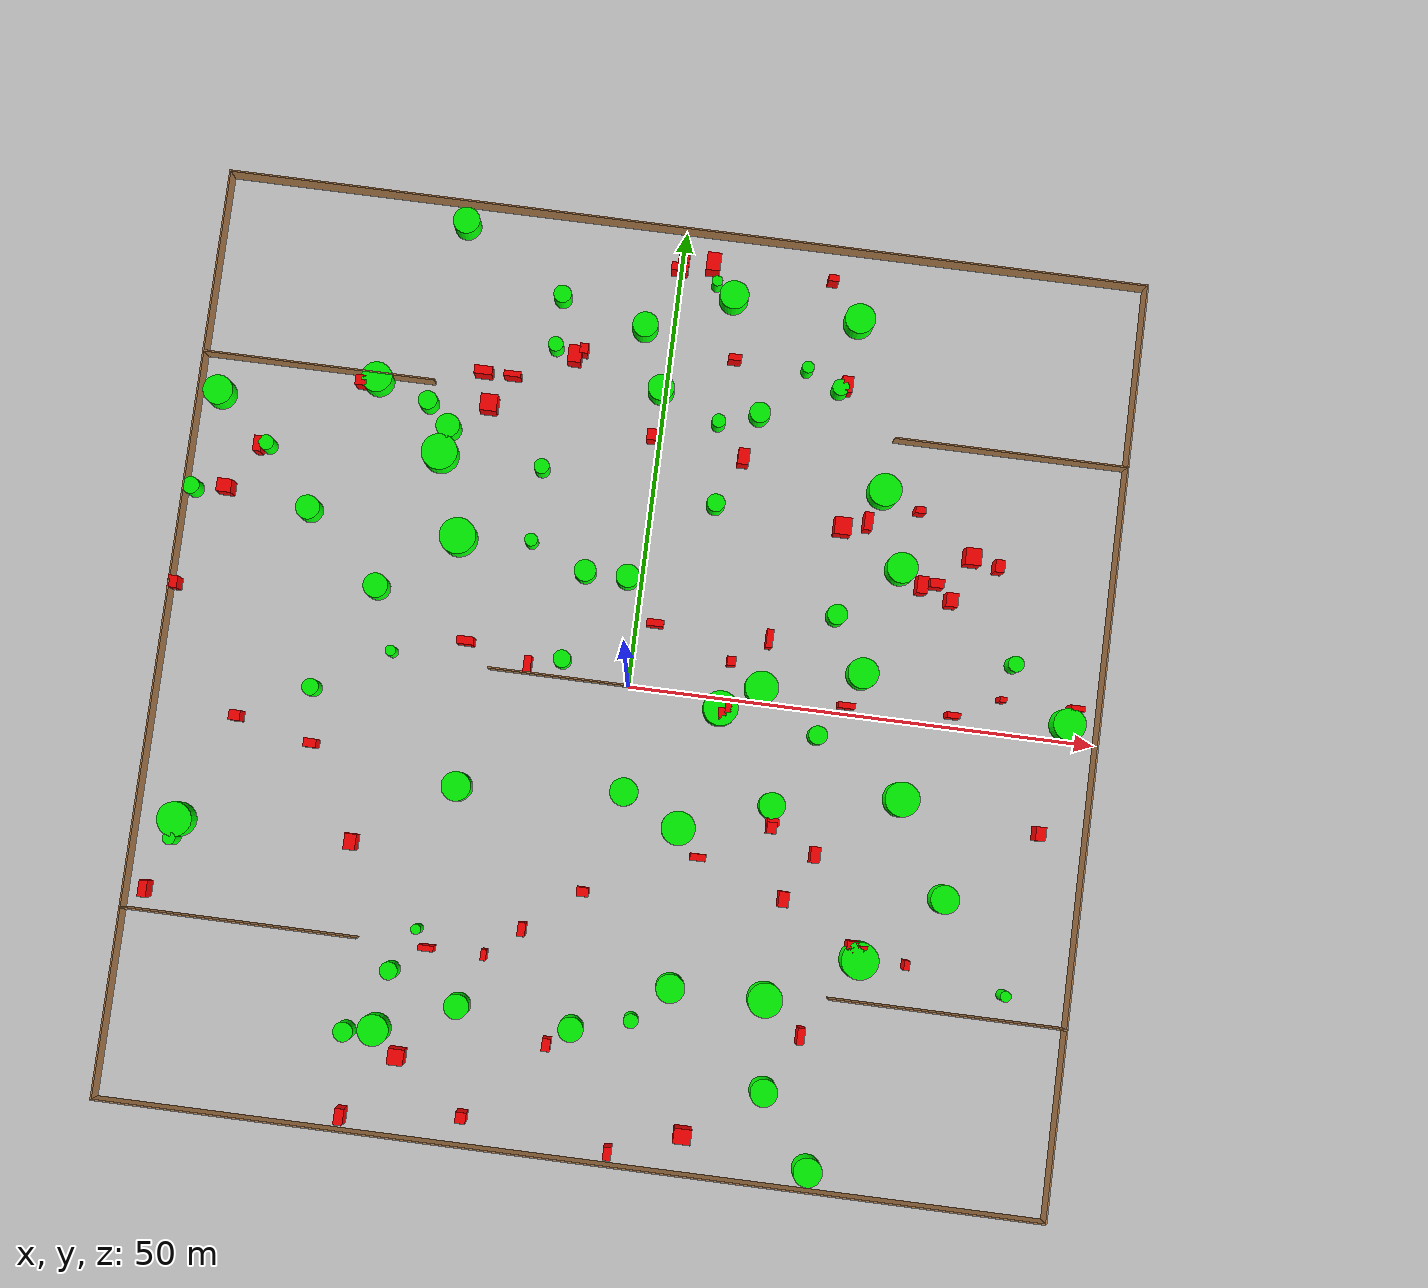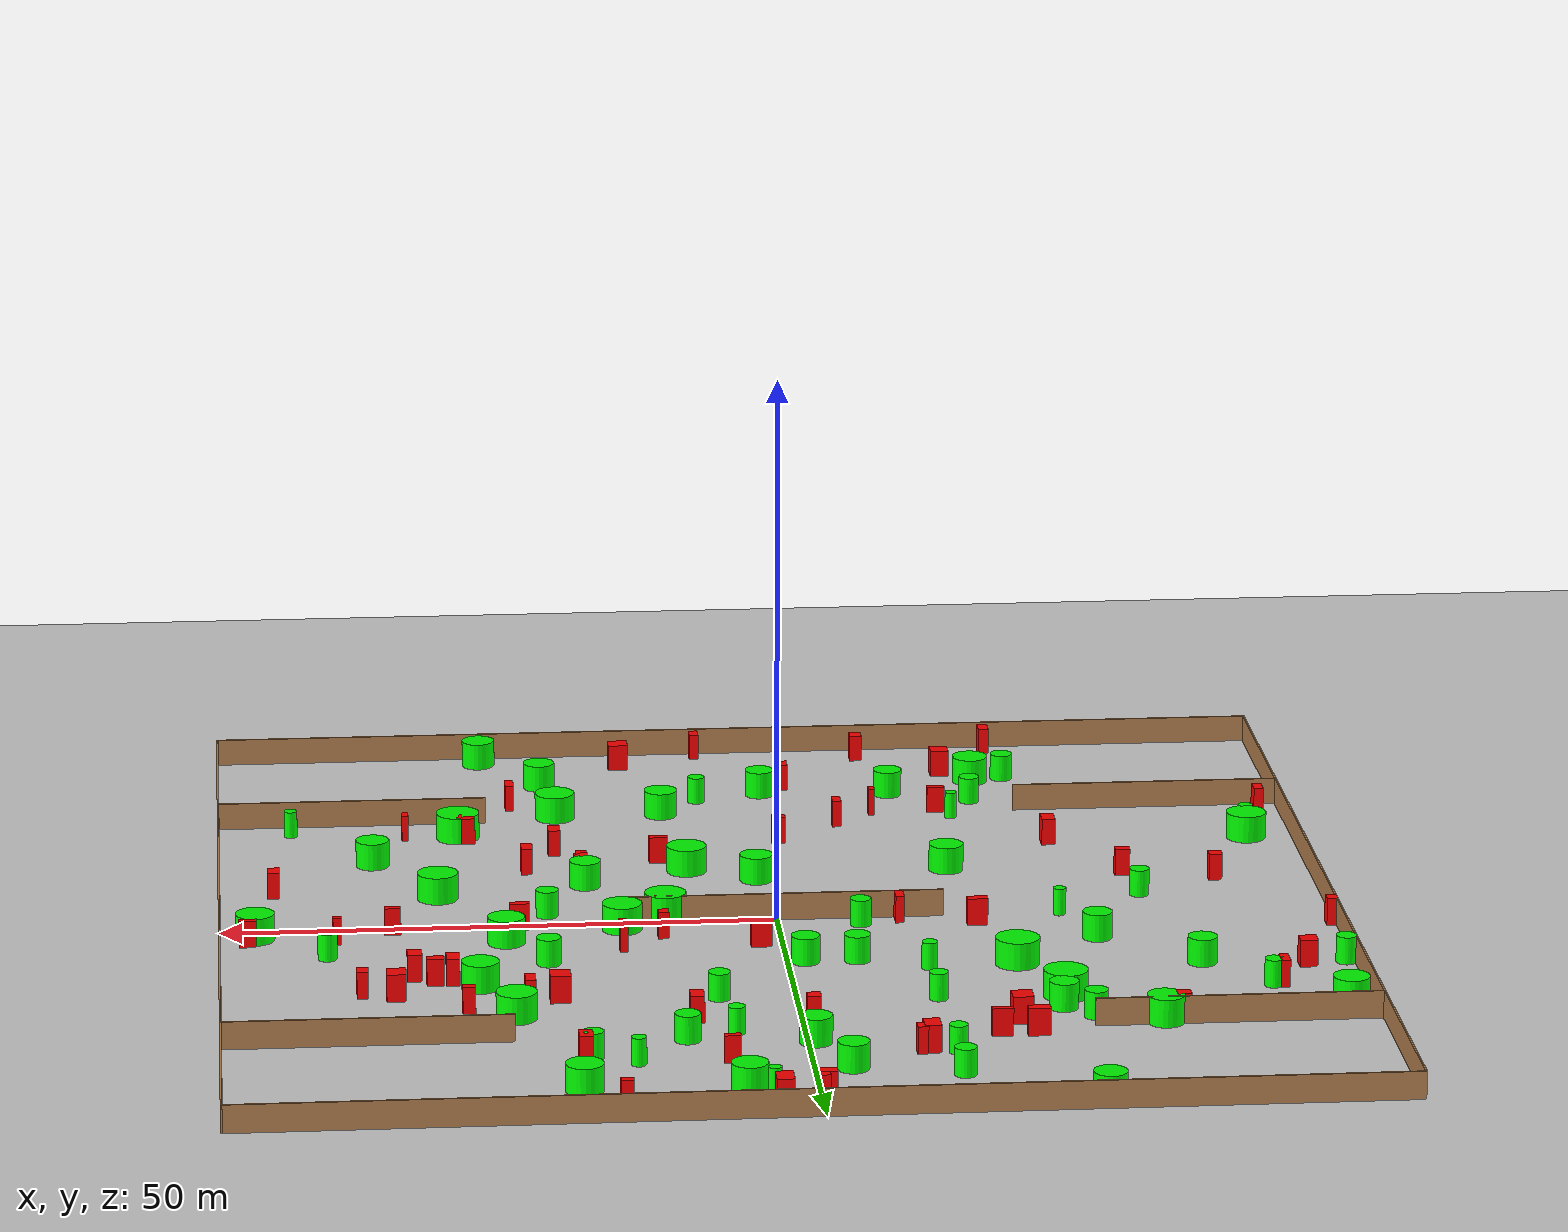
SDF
<sdf version="1.7">
 <world name="default">
  <light name="sun" type="directional">
   <pose>0 0 10 0 -0 0</pose>
   <diffuse>0.8 0.8 0.8 1</diffuse>
   <specular>0.2 0.2 0.2 1</specular>
   <attenuation>
    <range>1000</range>
    <constant>0.9</constant>
    <linear>0.01</linear>
    <quadratic>0.001</quadratic>
   </attenuation>
   <direction>-0.5 0.1 -0.9</direction>
   <spot><inner_angle>0</inner_angle><outer_angle>0</outer_angle><falloff>0</falloff></spot>
  </light>
  <model name="ground_plane">
   <static>1</static>
   <link name="link">
    <collision name="collision">
     <geometry><plane><normal>0 0 1</normal><size>100 100</size></plane></geometry>
     <surface>
      <contact><collide_bitmask>65535</collide_bitmask></contact>
      <friction><ode><mu>100</mu><mu2>50</mu2></ode></friction>
     </surface>
    </collision>
    <visual name="visual">
     <cast_shadows>0</cast_shadows>
     <geometry><plane><normal>0 0 1</normal><size>100 100</size></plane></geometry>
     <material>
      <script><uri>file://media/materials/scripts/gazebo.material</uri><name>Gazebo/Grey</name></script>
     </material>
    </visual>
   </link>
  </model>
  <gravity>0 0 -9.8</gravity>
  <magnetic_field>6e-06 2.3e-05 -4.2e-05</magnetic_field>
  <atmosphere type="adiabatic"/>
  <physics type="ode">
   <max_step_size>0.001</max_step_size>
   <real_time_factor>1</real_time_factor>
   <real_time_update_rate>1000</real_time_update_rate>
  </physics>
  <scene><ambient>0.4 0.4 0.4 1</ambient><background>0.7 0.7 0.7 1</background><shadows>1</shadows></scene>
  <spherical_coordinates>
   <surface_model>EARTH_WGS84</surface_model>
   <latitude_deg>0</latitude_deg>
   <longitude_deg>0</longitude_deg>
   <elevation>0</elevation>
   <heading_deg>0</heading_deg>
  </spherical_coordinates>
  <model name="my_base_walls">
   <link name="Wall_0">
    <collision name="Wall_0_Collision">
     <geometry><box><size>100.15 0.15 2.5</size></box></geometry>
     <pose>0 0 1.25 0 -0 0</pose>
    </collision>
    <visual name="Wall_0_Visual">
     <pose>0 0 1.25 0 -0 0</pose>
     <geometry><box><size>100.15 0.15 2.5</size></box></geometry>
     <material>
      <script><uri>file://media/materials/scripts/gazebo.material</uri><name>Gazebo/Wood</name></script>
      <ambient>1 1 1 1</ambient>
     </material>
     <meta><layer>0</layer></meta>
    </visual>
    <pose>0 -50 0 0 -0 0</pose>
   </link>
   <link name="Wall_10">
    <collision name="Wall_10_Collision">
     <geometry><box><size>25.15 0.15 2.5</size></box></geometry>
     <pose>0 0 1.25 0 -0 0</pose>
    </collision>
    <visual name="Wall_10_Visual">
     <pose>0 0 1.25 0 -0 0</pose>
     <geometry><box><size>25.15 0.15 2.5</size></box></geometry>
     <material>
      <script><uri>file://media/materials/scripts/gazebo.material</uri><name>Gazebo/Wood</name></script>
      <ambient>1 1 1 1</ambient>
     </material>
     <meta><layer>0</layer></meta>
    </visual>
    <pose>37.5 30 0 0 -0 0</pose>
   </link>
   <link name="Wall_12">
    <collision name="Wall_12_Collision">
     <geometry><box><size>25.15 0.15 2.5</size></box></geometry>
     <pose>0 0 1.25 0 -0 0</pose>
    </collision>
    <visual name="Wall_12_Visual">
     <pose>0 0 1.25 0 -0 0</pose>
     <geometry><box><size>25.15 0.15 2.5</size></box></geometry>
     <material>
      <script><uri>file://media/materials/scripts/gazebo.material</uri><name>Gazebo/Wood</name></script>
      <ambient>1 1 1 1</ambient>
     </material>
     <meta><layer>0</layer></meta>
    </visual>
    <pose>-37.5 -30 0 0 -0 0</pose>
   </link>
   <link name="Wall_14">
    <collision name="Wall_14_Collision">
     <geometry><box><size>25.15 0.15 2.5</size></box></geometry>
     <pose>0 0 1.25 0 -0 0</pose>
    </collision>
    <visual name="Wall_14_Visual">
     <pose>0 0 1.25 0 -0 0</pose>
     <geometry><box><size>25.15 0.15 2.5</size></box></geometry>
     <material>
      <script><uri>file://media/materials/scripts/gazebo.material</uri><name>Gazebo/Wood</name></script>
      <ambient>1 1 1 1</ambient>
     </material>
     <meta><layer>0</layer></meta>
    </visual>
    <pose>37.5 -30 0 0 -0 0</pose>
   </link>
   <link name="Wall_16">
    <collision name="Wall_16_Collision">
     <geometry><box><size>30.15 0.15 2.5</size></box></geometry>
     <pose>0 0 1.25 0 -0 0</pose>
    </collision>
    <visual name="Wall_16_Visual">
     <pose>0 0 1.25 0 -0 0</pose>
     <geometry><box><size>30.15 0.15 2.5</size></box></geometry>
     <material>
      <script><uri>file://media/materials/scripts/gazebo.material</uri><name>Gazebo/Wood</name></script>
      <ambient>1 1 1 1</ambient>
     </material>
     <meta><layer>0</layer></meta>
    </visual>
    <pose>0 0 0 0 -0 3.14159</pose>
   </link>
   <link name="Wall_2">
    <collision name="Wall_2_Collision">
     <geometry><box><size>100.15 0.15 2.5</size></box></geometry>
     <pose>0 0 1.25 0 -0 0</pose>
    </collision>
    <visual name="Wall_2_Visual">
     <pose>0 0 1.25 0 -0 0</pose>
     <geometry><box><size>100.15 0.15 2.5</size></box></geometry>
     <material>
      <script><uri>file://media/materials/scripts/gazebo.material</uri><name>Gazebo/Wood</name></script>
      <ambient>1 1 1 1</ambient>
     </material>
     <meta><layer>0</layer></meta>
    </visual>
    <pose>0 50 0 0 -0 3.14159</pose>
   </link>
   <link name="Wall_4">
    <collision name="Wall_4_Collision">
     <geometry><box><size>100.15 0.15 2.5</size></box></geometry>
     <pose>0 0 1.25 0 -0 0</pose>
    </collision>
    <visual name="Wall_4_Visual">
     <pose>0 0 1.25 0 -0 0</pose>
     <geometry><box><size>100.15 0.15 2.5</size></box></geometry>
     <material>
      <script><uri>file://media/materials/scripts/gazebo.material</uri><name>Gazebo/Wood</name></script>
      <ambient>1 1 1 1</ambient>
     </material>
     <meta><layer>0</layer></meta>
    </visual>
    <pose>50 0 0 0 -0 -1.5708</pose>
   </link>
   <link name="Wall_6">
    <collision name="Wall_6_Collision">
     <geometry><box><size>100.15 0.15 2.5</size></box></geometry>
     <pose>0 0 1.25 0 -0 0</pose>
    </collision>
    <visual name="Wall_6_Visual">
     <pose>0 0 1.25 0 -0 0</pose>
     <geometry><box><size>100.15 0.15 2.5</size></box></geometry>
     <material>
      <script><uri>file://media/materials/scripts/gazebo.material</uri><name>Gazebo/Wood</name></script>
      <ambient>1 1 1 1</ambient>
     </material>
     <meta><layer>0</layer></meta>
    </visual>
    <pose>-50 0 0 0 -0 1.5708</pose>
   </link>
   <link name="Wall_8">
    <collision name="Wall_8_Collision">
     <geometry><box><size>25.15 0.15 2.5</size></box></geometry>
     <pose>0 0 1.25 0 -0 0</pose>
    </collision>
    <visual name="Wall_8_Visual">
     <pose>0 0 1.25 0 -0 0</pose>
     <geometry><box><size>25.15 0.15 2.5</size></box></geometry>
     <material>
      <script><uri>file://media/materials/scripts/gazebo.material</uri><name>Gazebo/Wood</name></script>
      <ambient>1 1 1 1</ambient>
     </material>
     <meta><layer>0</layer></meta>
    </visual>
    <pose>-37.5 30 0 0 -0 0</pose>
   </link>
   <static>1</static>
  </model>
  <model name="cylinder1">
   <static>1</static>
   <link name="link">
    <inertial>
     <mass>1</mass>
     <inertia><ixx>0.5</ixx><ixy>0</ixy><ixz>0</ixz><iyy>0.5</iyy><iyz>0</iyz><izz>1</izz></inertia>
    </inertial>
    <collision name="collision">
     <geometry><cylinder><radius>1.8651</radius><length>2.5</length></cylinder></geometry>
    </collision>
    <visual name="visual">
     <geometry><cylinder><radius>1.8651</radius><length>2.5</length></cylinder></geometry>
     <material>
      <ambient>0 1 0 1</ambient>
      <diffuse>0 1 0 1</diffuse>
      <specular>0.1 0.1 0.1 1</specular>
      <emissive>0 0 0 0</emissive>
     </material>
    </visual>
   </link>
   <pose>30.1802 -8.29921 1.25 0 -0 0</pose>
  </model>
  <model name="cylinder2">
   <static>1</static>
   <link name="link">
    <inertial>
     <mass>1</mass>
     <inertia><ixx>0.5</ixx><ixy>0</ixy><ixz>0</ixz><iyy>0.5</iyy><iyz>0</iyz><izz>1</izz></inertia>
    </inertial>
    <collision name="collision">
     <geometry><cylinder><radius>0.702221</radius><length>2.5</length></cylinder></geometry>
    </collision>
    <visual name="visual">
     <geometry><cylinder><radius>0.702221</radius><length>2.5</length></cylinder></geometry>
     <material>
      <ambient>0 1 0 1</ambient>
      <diffuse>0 1 0 1</diffuse>
      <specular>0.1 0.1 0.1 1</specular>
      <emissive>0 0 0 0</emissive>
     </material>
    </visual>
   </link>
   <pose>-12.3186 14.1068 1.25 0 -0 0</pose>
  </model>
  <model name="cylinder3">
   <static>1</static>
   <link name="link">
    <inertial>
     <mass>1</mass>
     <inertia><ixx>0.5</ixx><ixy>0</ixy><ixz>0</ixz><iyy>0.5</iyy><iyz>0</iyz><izz>1</izz></inertia>
    </inertial>
    <collision name="collision">
     <geometry><cylinder><radius>1.09951</radius><length>2.5</length></cylinder></geometry>
    </collision>
    <visual name="visual">
     <geometry><cylinder><radius>1.09951</radius><length>2.5</length></cylinder></geometry>
     <material>
      <ambient>0 1 0 1</ambient>
      <diffuse>0 1 0 1</diffuse>
      <specular>0.1 0.1 0.1 1</specular>
      <emissive>0 0 0 0</emissive>
     </material>
    </visual>
   </link>
   <pose>21.0441 10.3055 1.25 0 -0 0</pose>
  </model>
  <model name="cylinder4">
   <static>1</static>
   <link name="link">
    <inertial>
     <mass>1</mass>
     <inertia><ixx>0.5</ixx><ixy>0</ixy><ixz>0</ixz><iyy>0.5</iyy><iyz>0</iyz><izz>1</izz></inertia>
    </inertial>
    <collision name="collision">
     <geometry><cylinder><radius>1.61484</radius><length>2.5</length></cylinder></geometry>
    </collision>
    <visual name="visual">
     <geometry><cylinder><radius>1.61484</radius><length>2.5</length></cylinder></geometry>
     <material>
      <ambient>0 1 0 1</ambient>
      <diffuse>0 1 0 1</diffuse>
      <specular>0.1 0.1 0.1 1</specular>
      <emissive>0 0 0 0</emissive>
     </material>
    </visual>
   </link>
   <pose>-47.8223 25.95 1.25 0 -0 0</pose>
  </model>
  <model name="cylinder5">
   <static>1</static>
   <link name="link">
    <inertial>
     <mass>1</mass>
     <inertia><ixx>0.5</ixx><ixy>0</ixy><ixz>0</ixz><iyy>0.5</iyy><iyz>0</iyz><izz>1</izz></inertia>
    </inertial>
    <collision name="collision">
     <geometry><cylinder><radius>1.2666</radius><length>2.5</length></cylinder></geometry>
    </collision>
    <visual name="visual">
     <geometry><cylinder><radius>1.2666</radius><length>2.5</length></cylinder></geometry>
     <material>
      <ambient>0 1 0 1</ambient>
      <diffuse>0 1 0 1</diffuse>
      <specular>0.1 0.1 0.1 1</specular>
      <emissive>0 0 0 0</emissive>
     </material>
    </visual>
   </link>
   <pose>-1.58055 11.573 1.25 0 -0 0</pose>
  </model>
  <model name="cylinder6">
   <static>1</static>
   <link name="link">
    <inertial>
     <mass>1</mass>
     <inertia><ixx>0.5</ixx><ixy>0</ixy><ixz>0</ixz><iyy>0.5</iyy><iyz>0</iyz><izz>1</izz></inertia>
    </inertial>
    <collision name="collision">
     <geometry><cylinder><radius>1.86456</radius><length>2.5</length></cylinder></geometry>
    </collision>
    <visual name="visual">
     <geometry><cylinder><radius>1.86456</radius><length>2.5</length></cylinder></geometry>
     <material>
      <ambient>0 1 0 1</ambient>
      <diffuse>0 1 0 1</diffuse>
      <specular>0.1 0.1 0.1 1</specular>
      <emissive>0 0 0 0</emissive>
     </material>
    </visual>
   </link>
   <pose>9.96198 -1.16739 1.25 0 -0 0</pose>
  </model>
  <model name="cylinder7">
   <static>1</static>
   <link name="link">
    <inertial>
     <mass>1</mass>
     <inertia><ixx>0.5</ixx><ixy>0</ixy><ixz>0</ixz><iyy>0.5</iyy><iyz>0</iyz><izz>1</izz></inertia>
    </inertial>
    <collision name="collision">
     <geometry><cylinder><radius>1.57269</radius><length>2.5</length></cylinder></geometry>
    </collision>
    <visual name="visual">
     <geometry><cylinder><radius>1.57269</radius><length>2.5</length></cylinder></geometry>
     <material>
      <ambient>0 1 0 1</ambient>
      <diffuse>0 1 0 1</diffuse>
      <specular>0.1 0.1 0.1 1</specular>
      <emissive>0 0 0 0</emissive>
     </material>
    </visual>
   </link>
   <pose>5.89837 43.3155 1.25 0 -0 0</pose>
  </model>
  <model name="cylinder8">
   <static>1</static>
   <link name="link">
    <inertial>
     <mass>1</mass>
     <inertia><ixx>0.5</ixx><ixy>0</ixy><ixz>0</ixz><iyy>0.5</iyy><iyz>0</iyz><izz>1</izz></inertia>
    </inertial>
    <collision name="collision">
     <geometry><cylinder><radius>1.33044</radius><length>2.5</length></cylinder></geometry>
    </collision>
    <visual name="visual">
     <geometry><cylinder><radius>1.33044</radius><length>2.5</length></cylinder></geometry>
     <material>
      <ambient>0 1 0 1</ambient>
      <diffuse>0 1 0 1</diffuse>
      <specular>0.1 0.1 0.1 1</specular>
      <emissive>0 0 0 0</emissive>
     </material>
    </visual>
   </link>
   <pose>-13.5744 -35.6998 1.25 0 -0 0</pose>
  </model>
  <model name="cylinder9">
   <static>1</static>
   <link name="link">
    <inertial>
     <mass>1</mass>
     <inertia><ixx>0.5</ixx><ixy>0</ixy><ixz>0</ixz><iyy>0.5</iyy><iyz>0</iyz><izz>1</izz></inertia>
    </inertial>
    <collision name="collision">
     <geometry><cylinder><radius>1.64942</radius><length>2.5</length></cylinder></geometry>
    </collision>
    <visual name="visual">
     <geometry><cylinder><radius>1.64942</radius><length>2.5</length></cylinder></geometry>
     <material>
      <ambient>0 1 0 1</ambient>
      <diffuse>0 1 0 1</diffuse>
      <specular>0.1 0.1 0.1 1</specular>
      <emissive>0 0 0 0</emissive>
     </material>
    </visual>
   </link>
   <pose>-21.8863 -39.2255 1.25 0 -0 0</pose>
  </model>
  <model name="cylinder10">
   <static>1</static>
   <link name="link">
    <inertial>
     <mass>1</mass>
     <inertia><ixx>0.5</ixx><ixy>0</ixy><ixz>0</ixz><iyy>0.5</iyy><iyz>0</iyz><izz>1</izz></inertia>
    </inertial>
    <collision name="collision">
     <geometry><cylinder><radius>0.595167</radius><length>2.5</length></cylinder></geometry>
    </collision>
    <visual name="visual">
     <geometry><cylinder><radius>0.595167</radius><length>2.5</length></cylinder></geometry>
     <material>
      <ambient>0 1 0 1</ambient>
      <diffuse>0 1 0 1</diffuse>
      <specular>0.1 0.1 0.1 1</specular>
      <emissive>0 0 0 0</emissive>
     </material>
    </visual>
   </link>
   <pose>43.251 -27.3612 1.25 0 -0 0</pose>
  </model>
  <model name="cylinder11">
   <static>1</static>
   <link name="link">
    <inertial>
     <mass>1</mass>
     <inertia><ixx>0.5</ixx><ixy>0</ixy><ixz>0</ixz><iyy>0.5</iyy><iyz>0</iyz><izz>1</izz></inertia>
    </inertial>
    <collision name="collision">
     <geometry><cylinder><radius>1.95467</radius><length>2.5</length></cylinder></geometry>
    </collision>
    <visual name="visual">
     <geometry><cylinder><radius>1.95467</radius><length>2.5</length></cylinder></geometry>
     <material>
      <ambient>0 1 0 1</ambient>
      <diffuse>0 1 0 1</diffuse>
      <specular>0.1 0.1 0.1 1</specular>
      <emissive>0 0 0 0</emissive>
     </material>
    </visual>
   </link>
   <pose>-23.3365 22.2974 1.25 0 -0 0</pose>
  </model>
  <model name="cylinder12">
   <static>1</static>
   <link name="link">
    <inertial>
     <mass>1</mass>
     <inertia><ixx>0.5</ixx><ixy>0</ixy><ixz>0</ixz><iyy>0.5</iyy><iyz>0</iyz><izz>1</izz></inertia>
    </inertial>
    <collision name="collision">
     <geometry><cylinder><radius>0.905594</radius><length>2.5</length></cylinder></geometry>
    </collision>
    <visual name="visual">
     <geometry><cylinder><radius>0.905594</radius><length>2.5</length></cylinder></geometry>
     <material>
      <ambient>0 1 0 1</ambient>
      <diffuse>0 1 0 1</diffuse>
      <specular>0.1 0.1 0.1 1</specular>
      <emissive>0 0 0 0</emissive>
     </material>
    </visual>
   </link>
   <pose>18.5045 34.7129 1.25 0 -0 0</pose>
  </model>
  <model name="cylinder13">
   <static>1</static>
   <link name="link">
    <inertial>
     <mass>1</mass>
     <inertia><ixx>0.5</ixx><ixy>0</ixy><ixz>0</ixz><iyy>0.5</iyy><iyz>0</iyz><izz>1</izz></inertia>
    </inertial>
    <collision name="collision">
     <geometry><cylinder><radius>1.41726</radius><length>2.5</length></cylinder></geometry>
    </collision>
    <visual name="visual">
     <geometry><cylinder><radius>1.41726</radius><length>2.5</length></cylinder></geometry>
     <material>
      <ambient>0 1 0 1</ambient>
      <diffuse>0 1 0 1</diffuse>
      <specular>0.1 0.1 0.1 1</specular>
      <emissive>0 0 0 0</emissive>
     </material>
    </visual>
   </link>
   <pose>16.6447 -10.7088 1.25 0 -0 0</pose>
  </model>
  <model name="cylinder14">
   <static>1</static>
   <link name="link">
    <inertial>
     <mass>1</mass>
     <inertia><ixx>0.5</ixx><ixy>0</ixy><ixz>0</ixz><iyy>0.5</iyy><iyz>0</iyz><izz>1</izz></inertia>
    </inertial>
    <collision name="collision">
     <geometry><cylinder><radius>1.02696</radius><length>2.5</length></cylinder></geometry>
    </collision>
    <visual name="visual">
     <geometry><cylinder><radius>1.02696</radius><length>2.5</length></cylinder></geometry>
     <material>
      <ambient>0 1 0 1</ambient>
      <diffuse>0 1 0 1</diffuse>
      <specular>0.1 0.1 0.1 1</specular>
      <emissive>0 0 0 0</emissive>
     </material>
    </visual>
   </link>
   <pose>-25.3086 27.6901 1.25 0 -0 0</pose>
  </model>
  <model name="cylinder15">
   <static>1</static>
   <link name="link">
    <inertial>
     <mass>1</mass>
     <inertia><ixx>0.5</ixx><ixy>0</ixy><ixz>0</ixz><iyy>0.5</iyy><iyz>0</iyz><izz>1</izz></inertia>
    </inertial>
    <collision name="collision">
     <geometry><cylinder><radius>1.97465</radius><length>2.5</length></cylinder></geometry>
    </collision>
    <visual name="visual">
     <geometry><cylinder><radius>1.97465</radius><length>2.5</length></cylinder></geometry>
     <material>
      <ambient>0 1 0 1</ambient>
      <diffuse>0 1 0 1</diffuse>
      <specular>0.1 0.1 0.1 1</specular>
      <emissive>0 0 0 0</emissive>
     </material>
    </visual>
   </link>
   <pose>-20.164 13.5504 1.25 0 -0 0</pose>
  </model>
  <model name="cylinder16">
   <static>1</static>
   <link name="link">
    <inertial>
     <mass>1</mass>
     <inertia><ixx>0.5</ixx><ixy>0</ixy><ixz>0</ixz><iyy>0.5</iyy><iyz>0</iyz><izz>1</izz></inertia>
    </inertial>
    <collision name="collision">
     <geometry><cylinder><radius>0.948958</radius><length>2.5</length></cylinder></geometry>
    </collision>
    <visual name="visual">
     <geometry><cylinder><radius>0.948958</radius><length>2.5</length></cylinder></geometry>
     <material>
      <ambient>0 1 0 1</ambient>
      <diffuse>0 1 0 1</diffuse>
      <specular>0.1 0.1 0.1 1</specular>
      <emissive>0 0 0 0</emissive>
     </material>
    </visual>
   </link>
   <pose>-21.0962 -32.9243 1.25 0 -0 0</pose>
  </model>
  <model name="cylinder17">
   <static>1</static>
   <link name="link">
    <inertial>
     <mass>1</mass>
     <inertia><ixx>0.5</ixx><ixy>0</ixy><ixz>0</ixz><iyy>0.5</iyy><iyz>0</iyz><izz>1</izz></inertia>
    </inertial>
    <collision name="collision">
     <geometry><cylinder><radius>0.568678</radius><length>2.5</length></cylinder></geometry>
    </collision>
    <visual name="visual">
     <geometry><cylinder><radius>0.568678</radius><length>2.5</length></cylinder></geometry>
     <material>
      <ambient>0 1 0 1</ambient>
      <diffuse>0 1 0 1</diffuse>
      <specular>0.1 0.1 0.1 1</specular>
      <emissive>0 0 0 0</emissive>
     </material>
    </visual>
   </link>
   <pose>3.90818 44.5877 1.25 0 -0 0</pose>
  </model>
  <model name="cylinder18">
   <static>1</static>
   <link name="link">
    <inertial>
     <mass>1</mass>
     <inertia><ixx>0.5</ixx><ixy>0</ixy><ixz>0</ixz><iyy>0.5</iyy><iyz>0</iyz><izz>1</izz></inertia>
    </inertial>
    <collision name="collision">
     <geometry><cylinder><radius>0.571479</radius><length>2.5</length></cylinder></geometry>
    </collision>
    <visual name="visual">
     <geometry><cylinder><radius>0.571479</radius><length>2.5</length></cylinder></geometry>
     <material>
      <ambient>0 1 0 1</ambient>
      <diffuse>0 1 0 1</diffuse>
      <specular>0.1 0.1 0.1 1</specular>
      <emissive>0 0 0 0</emissive>
     </material>
    </visual>
   </link>
   <pose>-25.548 0.445331 1.25 0 -0 0</pose>
  </model>
  <model name="cylinder19">
   <static>1</static>
   <link name="link">
    <inertial>
     <mass>1</mass>
     <inertia><ixx>0.5</ixx><ixy>0</ixy><ixz>0</ixz><iyy>0.5</iyy><iyz>0</iyz><izz>1</izz></inertia>
    </inertial>
    <collision name="collision">
     <geometry><cylinder><radius>1.04105</radius><length>2.5</length></cylinder></geometry>
    </collision>
    <visual name="visual">
     <geometry><cylinder><radius>1.04105</radius><length>2.5</length></cylinder></geometry>
     <material>
      <ambient>0 1 0 1</ambient>
      <diffuse>0 1 0 1</diffuse>
      <specular>0.1 0.1 0.1 1</specular>
      <emissive>0 0 0 0</emissive>
     </material>
    </visual>
   </link>
   <pose>-24.9636 -39.7891 1.25 0 -0 0</pose>
  </model>
  <model name="cylinder20">
   <static>1</static>
   <link name="link">
    <inertial>
     <mass>1</mass>
     <inertia><ixx>0.5</ixx><ixy>0</ixy><ixz>0</ixz><iyy>0.5</iyy><iyz>0</iyz><izz>1</izz></inertia>
    </inertial>
    <collision name="collision">
     <geometry><cylinder><radius>1.33759</radius><length>2.5</length></cylinder></geometry>
    </collision>
    <visual name="visual">
     <geometry><cylinder><radius>1.33759</radius><length>2.5</length></cylinder></geometry>
     <material>
      <ambient>0 1 0 1</ambient>
      <diffuse>0 1 0 1</diffuse>
      <specular>0.1 0.1 0.1 1</specular>
      <emissive>0 0 0 0</emissive>
     </material>
    </visual>
   </link>
   <pose>-28.1159 7.15874 1.25 0 -0 0</pose>
  </model>
  <model name="cylinder21">
   <static>1</static>
   <link name="link">
    <inertial>
     <mass>1</mass>
     <inertia><ixx>0.5</ixx><ixy>0</ixy><ixz>0</ixz><iyy>0.5</iyy><iyz>0</iyz><izz>1</izz></inertia>
    </inertial>
    <collision name="collision">
     <geometry><cylinder><radius>1.8193</radius><length>2.5</length></cylinder></geometry>
    </collision>
    <visual name="visual">
     <geometry><cylinder><radius>1.8193</radius><length>2.5</length></cylinder></geometry>
     <material>
      <ambient>0 1 0 1</ambient>
      <diffuse>0 1 0 1</diffuse>
      <specular>0.1 0.1 0.1 1</specular>
      <emissive>0 0 0 0</emissive>
     </material>
    </visual>
   </link>
   <pose>7.11333 -14.3212 1.25 0 -0 0</pose>
  </model>
  <model name="cylinder22">
   <static>1</static>
   <link name="link">
    <inertial>
     <mass>1</mass>
     <inertia><ixx>0.5</ixx><ixy>0</ixy><ixz>0</ixz><iyy>0.5</iyy><iyz>0</iyz><izz>1</izz></inertia>
    </inertial>
    <collision name="collision">
     <geometry><cylinder><radius>1.74425</radius><length>2.5</length></cylinder></geometry>
    </collision>
    <visual name="visual">
     <geometry><cylinder><radius>1.74425</radius><length>2.5</length></cylinder></geometry>
     <material>
      <ambient>0 1 0 1</ambient>
      <diffuse>0 1 0 1</diffuse>
      <specular>0.1 0.1 0.1 1</specular>
      <emissive>0 0 0 0</emissive>
     </material>
    </visual>
   </link>
   <pose>46.8099 1.81907 1.25 0 -0 0</pose>
  </model>
  <model name="cylinder23">
   <static>1</static>
   <link name="link">
    <inertial>
     <mass>1</mass>
     <inertia><ixx>0.5</ixx><ixy>0</ixy><ixz>0</ixz><iyy>0.5</iyy><iyz>0</iyz><izz>1</izz></inertia>
    </inertial>
    <collision name="collision">
     <geometry><cylinder><radius>1.13008</radius><length>2.5</length></cylinder></geometry>
    </collision>
    <visual name="visual">
     <geometry><cylinder><radius>1.13008</radius><length>2.5</length></cylinder></geometry>
     <material>
      <ambient>0 1 0 1</ambient>
      <diffuse>0 1 0 1</diffuse>
      <specular>0.1 0.1 0.1 1</specular>
      <emissive>0 0 0 0</emissive>
     </material>
    </visual>
   </link>
   <pose>10.2275 30.9059 1.25 0 -0 0</pose>
  </model>
  <model name="cylinder24">
   <static>1</static>
   <link name="link">
    <inertial>
     <mass>1</mass>
     <inertia><ixx>0.5</ixx><ixy>0</ixy><ixz>0</ixz><iyy>0.5</iyy><iyz>0</iyz><izz>1</izz></inertia>
    </inertial>
    <collision name="collision">
     <geometry><cylinder><radius>0.809136</radius><length>2.5</length></cylinder></geometry>
    </collision>
    <visual name="visual">
     <geometry><cylinder><radius>0.809136</radius><length>2.5</length></cylinder></geometry>
     <material>
      <ambient>0 1 0 1</ambient>
      <diffuse>0 1 0 1</diffuse>
      <specular>0.1 0.1 0.1 1</specular>
      <emissive>0 0 0 0</emissive>
     </material>
    </visual>
   </link>
   <pose>-12.4933 35.5216 1.25 0 -0 0</pose>
  </model>
  <model name="cylinder25">
   <static>1</static>
   <link name="link">
    <inertial>
     <mass>1</mass>
     <inertia><ixx>0.5</ixx><ixy>0</ixy><ixz>0</ixz><iyy>0.5</iyy><iyz>0</iyz><izz>1</izz></inertia>
    </inertial>
    <collision name="collision">
     <geometry><cylinder><radius>1.50995</radius><length>2.5</length></cylinder></geometry>
    </collision>
    <visual name="visual">
     <geometry><cylinder><radius>1.50995</radius><length>2.5</length></cylinder></geometry>
     <material>
      <ambient>0 1 0 1</ambient>
      <diffuse>0 1 0 1</diffuse>
      <specular>0.1 0.1 0.1 1</specular>
      <emissive>0 0 0 0</emissive>
     </material>
    </visual>
   </link>
   <pose>0.928293 -11.251 1.25 0 -0 0</pose>
  </model>
  <model name="cylinder26">
   <static>1</static>
   <link name="link">
    <inertial>
     <mass>1</mass>
     <inertia><ixx>0.5</ixx><ixy>0</ixy><ixz>0</ixz><iyy>0.5</iyy><iyz>0</iyz><izz>1</izz></inertia>
    </inertial>
    <collision name="collision">
     <geometry><cylinder><radius>0.654385</radius><length>2.5</length></cylinder></geometry>
    </collision>
    <visual name="visual">
     <geometry><cylinder><radius>0.654385</radius><length>2.5</length></cylinder></geometry>
     <material>
      <ambient>0 1 0 1</ambient>
      <diffuse>0 1 0 1</diffuse>
      <specular>0.1 0.1 0.1 1</specular>
      <emissive>0 0 0 0</emissive>
     </material>
    </visual>
   </link>
   <pose>14.7564 36.4573 1.25 0 -0 0</pose>
  </model>
  <model name="cylinder27">
   <static>1</static>
   <link name="link">
    <inertial>
     <mass>1</mass>
     <inertia><ixx>0.5</ixx><ixy>0</ixy><ixz>0</ixz><iyy>0.5</iyy><iyz>0</iyz><izz>1</izz></inertia>
    </inertial>
    <collision name="collision">
     <geometry><cylinder><radius>1.01462</radius><length>2.5</length></cylinder></geometry>
    </collision>
    <visual name="visual">
     <geometry><cylinder><radius>1.01462</radius><length>2.5</length></cylinder></geometry>
     <material>
      <ambient>0 1 0 1</ambient>
      <diffuse>0 1 0 1</diffuse>
      <specular>0.1 0.1 0.1 1</specular>
      <emissive>0 0 0 0</emissive>
     </material>
    </visual>
   </link>
   <pose>20.5325 -2.70864 1.25 0 -0 0</pose>
  </model>
  <model name="cylinder28">
   <static>1</static>
   <link name="link">
    <inertial>
     <mass>1</mass>
     <inertia><ixx>0.5</ixx><ixy>0</ixy><ixz>0</ixz><iyy>0.5</iyy><iyz>0</iyz><izz>1</izz></inertia>
    </inertial>
    <collision name="collision">
     <geometry><cylinder><radius>1.57902</radius><length>2.5</length></cylinder></geometry>
    </collision>
    <visual name="visual">
     <geometry><cylinder><radius>1.57902</radius><length>2.5</length></cylinder></geometry>
     <material>
      <ambient>0 1 0 1</ambient>
      <diffuse>0 1 0 1</diffuse>
      <specular>0.1 0.1 0.1 1</specular>
      <emissive>0 0 0 0</emissive>
     </material>
    </visual>
   </link>
   <pose>-16.72 -12.9216 1.25 0 -0 0</pose>
  </model>
  <model name="cylinder29">
   <static>1</static>
   <link name="link">
    <inertial>
     <mass>1</mass>
     <inertia><ixx>0.5</ixx><ixy>0</ixy><ixz>0</ixz><iyy>0.5</iyy><iyz>0</iyz><izz>1</izz></inertia>
    </inertial>
    <collision name="collision">
     <geometry><cylinder><radius>0.983032</radius><length>2.5</length></cylinder></geometry>
    </collision>
    <visual name="visual">
     <geometry><cylinder><radius>0.983032</radius><length>2.5</length></cylinder></geometry>
     <material>
      <ambient>0 1 0 1</ambient>
      <diffuse>0 1 0 1</diffuse>
      <specular>0.1 0.1 0.1 1</specular>
      <emissive>0 0 0 0</emissive>
     </material>
    </visual>
   </link>
   <pose>6.74331 20.5658 1.25 0 -0 0</pose>
  </model>
  <model name="cylinder30">
   <static>1</static>
   <link name="link">
    <inertial>
     <mass>1</mass>
     <inertia><ixx>0.5</ixx><ixy>0</ixy><ixz>0</ixz><iyy>0.5</iyy><iyz>0</iyz><izz>1</izz></inertia>
    </inertial>
    <collision name="collision">
     <geometry><cylinder><radius>1.84923</radius><length>2.5</length></cylinder></geometry>
    </collision>
    <visual name="visual">
     <geometry><cylinder><radius>1.84923</radius><length>2.5</length></cylinder></geometry>
     <material>
      <ambient>0 1 0 1</ambient>
      <diffuse>0 1 0 1</diffuse>
      <specular>0.1 0.1 0.1 1</specular>
      <emissive>0 0 0 0</emissive>
     </material>
    </visual>
   </link>
   <pose>-45.6889 -20.1189 1.25 0 -0 0</pose>
  </model>
  <model name="cylinder31">
   <static>1</static>
   <link name="link">
    <inertial>
     <mass>1</mass>
     <inertia><ixx>0.5</ixx><ixy>0</ixy><ixz>0</ixz><iyy>0.5</iyy><iyz>0</iyz><izz>1</izz></inertia>
    </inertial>
    <collision name="collision">
     <geometry><cylinder><radius>1.42699</radius><length>2.5</length></cylinder></geometry>
    </collision>
    <visual name="visual">
     <geometry><cylinder><radius>1.42699</radius><length>2.5</length></cylinder></geometry>
     <material>
      <ambient>0 1 0 1</ambient>
      <diffuse>0 1 0 1</diffuse>
      <specular>0.1 0.1 0.1 1</specular>
      <emissive>0 0 0 0</emissive>
     </material>
    </visual>
   </link>
   <pose>-0.639291 32.2517 1.25 0 -0 0</pose>
  </model>
  <model name="cylinder32">
   <static>1</static>
   <link name="link">
    <inertial>
     <mass>1</mass>
     <inertia><ixx>0.5</ixx><ixy>0</ixy><ixz>0</ixz><iyy>0.5</iyy><iyz>0</iyz><izz>1</izz></inertia>
    </inertial>
    <collision name="collision">
     <geometry><cylinder><radius>1.38813</radius><length>2.5</length></cylinder></geometry>
    </collision>
    <visual name="visual">
     <geometry><cylinder><radius>1.38813</radius><length>2.5</length></cylinder></geometry>
     <material>
      <ambient>0 1 0 1</ambient>
      <diffuse>0 1 0 1</diffuse>
      <specular>0.1 0.1 0.1 1</specular>
      <emissive>0 0 0 0</emissive>
     </material>
    </visual>
   </link>
   <pose>-3.20407 38.8674 1.25 0 -0 0</pose>
  </model>
  <model name="cylinder33">
   <static>1</static>
   <link name="link">
    <inertial>
     <mass>1</mass>
     <inertia><ixx>0.5</ixx><ixy>0</ixy><ixz>0</ixz><iyy>0.5</iyy><iyz>0</iyz><izz>1</izz></inertia>
    </inertial>
    <collision name="collision">
     <geometry><cylinder><radius>1.46466</radius><length>2.5</length></cylinder></geometry>
    </collision>
    <visual name="visual">
     <geometry><cylinder><radius>1.46466</radius><length>2.5</length></cylinder></geometry>
     <material>
      <ambient>0 1 0 1</ambient>
      <diffuse>0 1 0 1</diffuse>
      <specular>0.1 0.1 0.1 1</specular>
      <emissive>0 0 0 0</emissive>
     </material>
    </visual>
   </link>
   <pose>19.4033 -40.4297 1.25 0 -0 0</pose>
  </model>
  <model name="cylinder34">
   <static>1</static>
   <link name="link">
    <inertial>
     <mass>1</mass>
     <inertia><ixx>0.5</ixx><ixy>0</ixy><ixz>0</ixz><iyy>0.5</iyy><iyz>0</iyz><izz>1</izz></inertia>
    </inertial>
    <collision name="collision">
     <geometry><cylinder><radius>1.66903</radius><length>2.5</length></cylinder></geometry>
    </collision>
    <visual name="visual">
     <geometry><cylinder><radius>1.66903</radius><length>2.5</length></cylinder></geometry>
     <material>
      <ambient>0 1 0 1</ambient>
      <diffuse>0 1 0 1</diffuse>
      <specular>0.1 0.1 0.1 1</specular>
      <emissive>0 0 0 0</emissive>
     </material>
    </visual>
   </link>
   <pose>27.3196 16.1645 1.25 0 -0 0</pose>
  </model>
  <model name="cylinder35">
   <static>1</static>
   <link name="link">
    <inertial>
     <mass>1</mass>
     <inertia><ixx>0.5</ixx><ixy>0</ixy><ixz>0</ixz><iyy>0.5</iyy><iyz>0</iyz><izz>1</izz></inertia>
    </inertial>
    <collision name="collision">
     <geometry><cylinder><radius>1.99395</radius><length>2.5</length></cylinder></geometry>
    </collision>
    <visual name="visual">
     <geometry><cylinder><radius>1.99395</radius><length>2.5</length></cylinder></geometry>
     <material>
      <ambient>0 1 0 1</ambient>
      <diffuse>0 1 0 1</diffuse>
      <specular>0.1 0.1 0.1 1</specular>
      <emissive>0 0 0 0</emissive>
     </material>
    </visual>
   </link>
   <pose>27.7227 -25.6341 1.25 0 -0 0</pose>
  </model>
  <model name="cylinder36">
   <static>1</static>
   <link name="link">
    <inertial>
     <mass>1</mass>
     <inertia><ixx>0.5</ixx><ixy>0</ixy><ixz>0</ixz><iyy>0.5</iyy><iyz>0</iyz><izz>1</izz></inertia>
    </inertial>
    <collision name="collision">
     <geometry><cylinder><radius>1.31027</radius><length>2.5</length></cylinder></geometry>
    </collision>
    <visual name="visual">
     <geometry><cylinder><radius>1.31027</radius><length>2.5</length></cylinder></geometry>
     <material>
      <ambient>0 1 0 1</ambient>
      <diffuse>0 1 0 1</diffuse>
      <specular>0.1 0.1 0.1 1</specular>
      <emissive>0 0 0 0</emissive>
     </material>
    </visual>
   </link>
   <pose>-36.4623 14.5622 1.25 0 -0 0</pose>
  </model>
  <model name="cylinder37">
   <static>1</static>
   <link name="link">
    <inertial>
     <mass>1</mass>
     <inertia><ixx>0.5</ixx><ixy>0</ixy><ixz>0</ixz><iyy>0.5</iyy><iyz>0</iyz><izz>1</izz></inertia>
    </inertial>
    <collision name="collision">
     <geometry><cylinder><radius>0.948377</radius><length>2.5</length></cylinder></geometry>
    </collision>
    <visual name="visual">
     <geometry><cylinder><radius>0.948377</radius><length>2.5</length></cylinder></geometry>
     <material>
      <ambient>0 1 0 1</ambient>
      <diffuse>0 1 0 1</diffuse>
      <specular>0.1 0.1 0.1 1</specular>
      <emissive>0 0 0 0</emissive>
     </material>
    </visual>
   </link>
   <pose>-7.38881 1.90817 1.25 0 -0 0</pose>
  </model>
  <model name="cylinder38">
   <static>1</static>
   <link name="link">
    <inertial>
     <mass>1</mass>
     <inertia><ixx>0.5</ixx><ixy>0</ixy><ixz>0</ixz><iyy>0.5</iyy><iyz>0</iyz><izz>1</izz></inertia>
    </inertial>
    <collision name="collision">
     <geometry><cylinder><radius>0.747737</radius><length>2.5</length></cylinder></geometry>
    </collision>
    <visual name="visual">
     <geometry><cylinder><radius>0.747737</radius><length>2.5</length></cylinder></geometry>
     <material>
      <ambient>0 1 0 1</ambient>
      <diffuse>0 1 0 1</diffuse>
      <specular>0.1 0.1 0.1 1</specular>
      <emissive>0 0 0 0</emissive>
     </material>
    </visual>
   </link>
   <pose>5.94157 29.4359 1.25 0 -0 0</pose>
  </model>
  <model name="cylinder39">
   <static>1</static>
   <link name="link">
    <inertial>
     <mass>1</mass>
     <inertia><ixx>0.5</ixx><ixy>0</ixy><ixz>0</ixz><iyy>0.5</iyy><iyz>0</iyz><izz>1</izz></inertia>
    </inertial>
    <collision name="collision">
     <geometry><cylinder><radius>1.78702</radius><length>2.5</length></cylinder></geometry>
    </collision>
    <visual name="visual">
     <geometry><cylinder><radius>1.78702</radius><length>2.5</length></cylinder></geometry>
     <material>
      <ambient>0 1 0 1</ambient>
      <diffuse>0 1 0 1</diffuse>
      <specular>0.1 0.1 0.1 1</specular>
      <emissive>0 0 0 0</emissive>
     </material>
    </visual>
   </link>
   <pose>24.5307 24.2606 1.25 0 -0 0</pose>
  </model>
  <model name="cylinder40">
   <static>1</static>
   <link name="link">
    <inertial>
     <mass>1</mass>
     <inertia><ixx>0.5</ixx><ixy>0</ixy><ixz>0</ixz><iyy>0.5</iyy><iyz>0</iyz><izz>1</izz></inertia>
    </inertial>
    <collision name="collision">
     <geometry><cylinder><radius>0.834806</radius><length>2.5</length></cylinder></geometry>
    </collision>
    <visual name="visual">
     <geometry><cylinder><radius>0.834806</radius><length>2.5</length></cylinder></geometry>
     <material>
      <ambient>0 1 0 1</ambient>
      <diffuse>0 1 0 1</diffuse>
      <specular>0.1 0.1 0.1 1</specular>
      <emissive>0 0 0 0</emissive>
     </material>
    </visual>
   </link>
   <pose>-12.2509 22.1219 1.25 0 -0 0</pose>
  </model>
  <model name="cylinder41">
   <static>1</static>
   <link name="link">
    <inertial>
     <mass>1</mass>
     <inertia><ixx>0.5</ixx><ixy>0</ixy><ixz>0</ixz><iyy>0.5</iyy><iyz>0</iyz><izz>1</izz></inertia>
    </inertial>
    <collision name="collision">
     <geometry><cylinder><radius>1.65017</radius><length>2.5</length></cylinder></geometry>
    </collision>
    <visual name="visual">
     <geometry><cylinder><radius>1.65017</radius><length>2.5</length></cylinder></geometry>
     <material>
      <ambient>0 1 0 1</ambient>
      <diffuse>0 1 0 1</diffuse>
      <specular>0.1 0.1 0.1 1</specular>
      <emissive>0 0 0 0</emissive>
     </material>
    </visual>
   </link>
   <pose>19.6859 42.4461 1.25 0 -0 0</pose>
  </model>
  <model name="cylinder42">
   <static>1</static>
   <link name="link">
    <inertial>
     <mass>1</mass>
     <inertia><ixx>0.5</ixx><ixy>0</ixy><ixz>0</ixz><iyy>0.5</iyy><iyz>0</iyz><izz>1</izz></inertia>
    </inertial>
    <collision name="collision">
     <geometry><cylinder><radius>0.829113</radius><length>2.5</length></cylinder></geometry>
    </collision>
    <visual name="visual">
     <geometry><cylinder><radius>0.829113</radius><length>2.5</length></cylinder></geometry>
     <material>
      <ambient>0 1 0 1</ambient>
      <diffuse>0 1 0 1</diffuse>
      <specular>0.1 0.1 0.1 1</specular>
      <emissive>0 0 0 0</emissive>
     </material>
    </visual>
   </link>
   <pose>-41.8412 20.926 1.25 0 -0 0</pose>
  </model>
  <model name="cylinder43">
   <static>1</static>
   <link name="link">
    <inertial>
     <mass>1</mass>
     <inertia><ixx>0.5</ixx><ixy>0</ixy><ixz>0</ixz><iyy>0.5</iyy><iyz>0</iyz><izz>1</izz></inertia>
    </inertial>
    <collision name="collision">
     <geometry><cylinder><radius>1.29225</radius><length>2.5</length></cylinder></geometry>
    </collision>
    <visual name="visual">
     <geometry><cylinder><radius>1.29225</radius><length>2.5</length></cylinder></geometry>
     <material>
      <ambient>0 1 0 1</ambient>
      <diffuse>0 1 0 1</diffuse>
      <specular>0.1 0.1 0.1 1</specular>
      <emissive>0 0 0 0</emissive>
     </material>
    </visual>
   </link>
   <pose>-22.8063 25.2349 1.25 0 -0 0</pose>
  </model>
  <model name="cylinder44">
   <static>1</static>
   <link name="link">
    <inertial>
     <mass>1</mass>
     <inertia><ixx>0.5</ixx><ixy>0</ixy><ixz>0</ixz><iyy>0.5</iyy><iyz>0</iyz><izz>1</izz></inertia>
    </inertial>
    <collision name="collision">
     <geometry><cylinder><radius>1.53328</radius><length>2.5</length></cylinder></geometry>
    </collision>
    <visual name="visual">
     <geometry><cylinder><radius>1.53328</radius><length>2.5</length></cylinder></geometry>
     <material>
      <ambient>0 1 0 1</ambient>
      <diffuse>0 1 0 1</diffuse>
      <specular>0.1 0.1 0.1 1</specular>
      <emissive>0 0 0 0</emissive>
     </material>
    </visual>
   </link>
   <pose>35.838 -18.1699 1.25 0 -0 0</pose>
  </model>
  <model name="cylinder45">
   <static>1</static>
   <link name="link">
    <inertial>
     <mass>1</mass>
     <inertia><ixx>0.5</ixx><ixy>0</ixy><ixz>0</ixz><iyy>0.5</iyy><iyz>0</iyz><izz>1</izz></inertia>
    </inertial>
    <collision name="collision">
     <geometry><cylinder><radius>0.860562</radius><length>2.5</length></cylinder></geometry>
    </collision>
    <visual name="visual">
     <geometry><cylinder><radius>0.860562</radius><length>2.5</length></cylinder></geometry>
     <material>
      <ambient>0 1 0 1</ambient>
      <diffuse>0 1 0 1</diffuse>
      <specular>0.1 0.1 0.1 1</specular>
      <emissive>0 0 0 0</emissive>
     </material>
    </visual>
   </link>
   <pose>40.4796 7.45677 1.25 0 -0 0</pose>
  </model>
  <model name="cylinder46">
   <static>1</static>
   <link name="link">
    <inertial>
     <mass>1</mass>
     <inertia><ixx>0.5</ixx><ixy>0</ixy><ixz>0</ixz><iyy>0.5</iyy><iyz>0</iyz><izz>1</izz></inertia>
    </inertial>
    <collision name="collision">
     <geometry><cylinder><radius>1.45436</radius><length>2.5</length></cylinder></geometry>
    </collision>
    <visual name="visual">
     <geometry><cylinder><radius>1.45436</radius><length>2.5</length></cylinder></geometry>
     <material>
      <ambient>0 1 0 1</ambient>
      <diffuse>0 1 0 1</diffuse>
      <specular>0.1 0.1 0.1 1</specular>
      <emissive>0 0 0 0</emissive>
     </material>
    </visual>
   </link>
   <pose>-23.8486 47.7871 1.25 0 -0 0</pose>
  </model>
  <model name="cylinder47">
   <static>1</static>
   <link name="link">
    <inertial>
     <mass>1</mass>
     <inertia><ixx>0.5</ixx><ixy>0</ixy><ixz>0</ixz><iyy>0.5</iyy><iyz>0</iyz><izz>1</izz></inertia>
    </inertial>
    <collision name="collision">
     <geometry><cylinder><radius>0.969003</radius><length>2.5</length></cylinder></geometry>
    </collision>
    <visual name="visual">
     <geometry><cylinder><radius>0.969003</radius><length>2.5</length></cylinder></geometry>
     <material>
      <ambient>0 1 0 1</ambient>
      <diffuse>0 1 0 1</diffuse>
      <specular>0.1 0.1 0.1 1</specular>
      <emissive>0 0 0 0</emissive>
     </material>
    </visual>
   </link>
   <pose>-12.4816 41.0566 1.25 0 -0 0</pose>
  </model>
  <model name="cylinder48">
   <static>1</static>
   <link name="link">
    <inertial>
     <mass>1</mass>
     <inertia><ixx>0.5</ixx><ixy>0</ixy><ixz>0</ixz><iyy>0.5</iyy><iyz>0</iyz><izz>1</izz></inertia>
    </inertial>
    <collision name="collision">
     <geometry><cylinder><radius>1.64987</radius><length>2.5</length></cylinder></geometry>
    </collision>
    <visual name="visual">
     <geometry><cylinder><radius>1.64987</radius><length>2.5</length></cylinder></geometry>
     <material>
      <ambient>0 1 0 1</ambient>
      <diffuse>0 1 0 1</diffuse>
      <specular>0.1 0.1 0.1 1</specular>
      <emissive>0 0 0 0</emissive>
     </material>
    </visual>
   </link>
   <pose>-31.1012 29.4985 1.25 0 -0 0</pose>
  </model>
  <model name="cylinder49">
   <static>1</static>
   <link name="link">
    <inertial>
     <mass>1</mass>
     <inertia><ixx>0.5</ixx><ixy>0</ixy><ixz>0</ixz><iyy>0.5</iyy><iyz>0</iyz><izz>1</izz></inertia>
    </inertial>
    <collision name="collision">
     <geometry><cylinder><radius>0.902289</radius><length>2.5</length></cylinder></geometry>
    </collision>
    <visual name="visual">
     <geometry><cylinder><radius>0.902289</radius><length>2.5</length></cylinder></geometry>
     <material>
      <ambient>0 1 0 1</ambient>
      <diffuse>0 1 0 1</diffuse>
      <specular>0.1 0.1 0.1 1</specular>
      <emissive>0 0 0 0</emissive>
     </material>
    </visual>
   </link>
   <pose>-33.4644 -4.46645 1.25 0 -0 0</pose>
  </model>
  <model name="cylinder50">
   <static>1</static>
   <link name="link">
    <inertial>
     <mass>1</mass>
     <inertia><ixx>0.5</ixx><ixy>0</ixy><ixz>0</ixz><iyy>0.5</iyy><iyz>0</iyz><izz>1</izz></inertia>
    </inertial>
    <collision name="collision">
     <geometry><cylinder><radius>1.1804</radius><length>2.5</length></cylinder></geometry>
    </collision>
    <visual name="visual">
     <geometry><cylinder><radius>1.1804</radius><length>2.5</length></cylinder></geometry>
     <material>
      <ambient>0 1 0 1</ambient>
      <diffuse>0 1 0 1</diffuse>
      <specular>0.1 0.1 0.1 1</specular>
      <emissive>0 0 0 0</emissive>
     </material>
    </visual>
   </link>
   <pose>-6.17269 11.5724 1.25 0 -0 0</pose>
  </model>
  <model name="cylinder51">
   <static>1</static>
   <link name="link">
    <inertial>
     <mass>1</mass>
     <inertia><ixx>0.5</ixx><ixy>0</ixy><ixz>0</ixz><iyy>0.5</iyy><iyz>0</iyz><izz>1</izz></inertia>
    </inertial>
    <collision name="collision">
     <geometry><cylinder><radius>1.79431</radius><length>2.5</length></cylinder></geometry>
    </collision>
    <visual name="visual">
     <geometry><cylinder><radius>1.79431</radius><length>2.5</length></cylinder></geometry>
     <material>
      <ambient>0 1 0 1</ambient>
      <diffuse>0 1 0 1</diffuse>
      <specular>0.1 0.1 0.1 1</specular>
      <emissive>0 0 0 0</emissive>
     </material>
    </visual>
   </link>
   <pose>14.031 1.5401 1.25 0 -0 0</pose>
  </model>
  <model name="cylinder52">
   <static>1</static>
   <link name="link">
    <inertial>
     <mass>1</mass>
     <inertia><ixx>0.5</ixx><ixy>0</ixy><ixz>0</ixz><iyy>0.5</iyy><iyz>0</iyz><izz>1</izz></inertia>
    </inertial>
    <collision name="collision">
     <geometry><cylinder><radius>1.85071</radius><length>2.5</length></cylinder></geometry>
    </collision>
    <visual name="visual">
     <geometry><cylinder><radius>1.85071</radius><length>2.5</length></cylinder></geometry>
     <material>
      <ambient>0 1 0 1</ambient>
      <diffuse>0 1 0 1</diffuse>
      <specular>0.1 0.1 0.1 1</specular>
      <emissive>0 0 0 0</emissive>
     </material>
    </visual>
   </link>
   <pose>18.378 -30.9505 1.25 0 -0 0</pose>
  </model>
  <model name="cylinder53">
   <static>1</static>
   <link name="link">
    <inertial>
     <mass>1</mass>
     <inertia><ixx>0.5</ixx><ixy>0</ixy><ixz>0</ixz><iyy>0.5</iyy><iyz>0</iyz><izz>1</izz></inertia>
    </inertial>
    <collision name="collision">
     <geometry><cylinder><radius>1.54016</radius><length>2.5</length></cylinder></geometry>
    </collision>
    <visual name="visual">
     <geometry><cylinder><radius>1.54016</radius><length>2.5</length></cylinder></geometry>
     <material>
      <ambient>0 1 0 1</ambient>
      <diffuse>0 1 0 1</diffuse>
      <specular>0.1 0.1 0.1 1</specular>
      <emissive>0 0 0 0</emissive>
     </material>
    </visual>
   </link>
   <pose>24.9018 -47.9278 1.25 0 -0 0</pose>
  </model>
  <model name="cylinder54">
   <static>1</static>
   <link name="link">
    <inertial>
     <mass>1</mass>
     <inertia><ixx>0.5</ixx><ixy>0</ixy><ixz>0</ixz><iyy>0.5</iyy><iyz>0</iyz><izz>1</izz></inertia>
    </inertial>
    <collision name="collision">
     <geometry><cylinder><radius>0.543402</radius><length>2.5</length></cylinder></geometry>
    </collision>
    <visual name="visual">
     <geometry><cylinder><radius>0.543402</radius><length>2.5</length></cylinder></geometry>
     <material>
      <ambient>0 1 0 1</ambient>
      <diffuse>0 1 0 1</diffuse>
      <specular>0.1 0.1 0.1 1</specular>
      <emissive>0 0 0 0</emissive>
     </material>
    </visual>
   </link>
   <pose>-18.8511 -28.2916 1.25 0 -0 0</pose>
  </model>
  <model name="cylinder55">
   <static>1</static>
   <link name="link">
    <inertial>
     <mass>1</mass>
     <inertia><ixx>0.5</ixx><ixy>0</ixy><ixz>0</ixz><iyy>0.5</iyy><iyz>0</iyz><izz>1</izz></inertia>
    </inertial>
    <collision name="collision">
     <geometry><cylinder><radius>0.782471</radius><length>2.5</length></cylinder></geometry>
    </collision>
    <visual name="visual">
     <geometry><cylinder><radius>0.782471</radius><length>2.5</length></cylinder></geometry>
     <material>
      <ambient>0 1 0 1</ambient>
      <diffuse>0 1 0 1</diffuse>
      <specular>0.1 0.1 0.1 1</specular>
      <emissive>0 0 0 0</emissive>
     </material>
    </visual>
   </link>
   <pose>4.72557 -34.8483 1.25 0 -0 0</pose>
  </model>
  <model name="cylinder56">
   <static>1</static>
   <link name="link">
    <inertial>
     <mass>1</mass>
     <inertia><ixx>0.5</ixx><ixy>0</ixy><ixz>0</ixz><iyy>0.5</iyy><iyz>0</iyz><izz>1</izz></inertia>
    </inertial>
    <collision name="collision">
     <geometry><cylinder><radius>1.53311</radius><length>2.5</length></cylinder></geometry>
    </collision>
    <visual name="visual">
     <geometry><cylinder><radius>1.53311</radius><length>2.5</length></cylinder></geometry>
     <material>
      <ambient>0 1 0 1</ambient>
      <diffuse>0 1 0 1</diffuse>
      <specular>0.1 0.1 0.1 1</specular>
      <emissive>0 0 0 0</emissive>
     </material>
    </visual>
   </link>
   <pose>8.37751 -31.0098 1.25 0 -0 0</pose>
  </model>
  <model name="cylinder57">
   <static>1</static>
   <link name="link">
    <inertial>
     <mass>1</mass>
     <inertia><ixx>0.5</ixx><ixy>0</ixy><ixz>0</ixz><iyy>0.5</iyy><iyz>0</iyz><izz>1</izz></inertia>
    </inertial>
    <collision name="collision">
     <geometry><cylinder><radius>1.67014</radius><length>2.5</length></cylinder></geometry>
    </collision>
    <visual name="visual">
     <geometry><cylinder><radius>1.67014</radius><length>2.5</length></cylinder></geometry>
     <material>
      <ambient>0 1 0 1</ambient>
      <diffuse>0 1 0 1</diffuse>
      <specular>0.1 0.1 0.1 1</specular>
      <emissive>0 0 0 0</emissive>
     </material>
    </visual>
   </link>
   <pose>24.5219 4.44485 1.25 0 -0 0</pose>
  </model>
  <model name="cylinder58">
   <static>1</static>
   <link name="link">
    <inertial>
     <mass>1</mass>
     <inertia><ixx>0.5</ixx><ixy>0</ixy><ixz>0</ixz><iyy>0.5</iyy><iyz>0</iyz><izz>1</izz></inertia>
    </inertial>
    <collision name="collision">
     <geometry><cylinder><radius>0.681296</radius><length>2.5</length></cylinder></geometry>
    </collision>
    <visual name="visual">
     <geometry><cylinder><radius>0.681296</radius><length>2.5</length></cylinder></geometry>
     <material>
      <ambient>0 1 0 1</ambient>
      <diffuse>0 1 0 1</diffuse>
      <specular>0.1 0.1 0.1 1</specular>
      <emissive>0 0 0 0</emissive>
     </material>
    </visual>
   </link>
   <pose>-45.9335 -22.1679 1.25 0 -0 0</pose>
  </model>
  <model name="cylinder59">
   <static>1</static>
   <link name="link">
    <inertial>
     <mass>1</mass>
     <inertia><ixx>0.5</ixx><ixy>0</ixy><ixz>0</ixz><iyy>0.5</iyy><iyz>0</iyz><izz>1</izz></inertia>
    </inertial>
    <collision name="collision">
     <geometry><cylinder><radius>1.32999</radius><length>2.5</length></cylinder></geometry>
    </collision>
    <visual name="visual">
     <geometry><cylinder><radius>1.32999</radius><length>2.5</length></cylinder></geometry>
     <material>
      <ambient>0 1 0 1</ambient>
      <diffuse>0 1 0 1</diffuse>
      <specular>0.1 0.1 0.1 1</specular>
      <emissive>0 0 0 0</emissive>
     </material>
    </visual>
   </link>
   <pose>-1.41158 -36.5224 1.25 0 -0 0</pose>
  </model>
  <model name="cylinder60">
   <static>1</static>
   <link name="link">
    <inertial>
     <mass>1</mass>
     <inertia><ixx>0.5</ixx><ixy>0</ixy><ixz>0</ixz><iyy>0.5</iyy><iyz>0</iyz><izz>1</izz></inertia>
    </inertial>
    <collision name="collision">
     <geometry><cylinder><radius>0.918252</radius><length>2.5</length></cylinder></geometry>
    </collision>
    <visual name="visual">
     <geometry><cylinder><radius>0.918252</radius><length>2.5</length></cylinder></geometry>
     <material>
      <ambient>0 1 0 1</ambient>
      <diffuse>0 1 0 1</diffuse>
      <specular>0.1 0.1 0.1 1</specular>
      <emissive>0 0 0 0</emissive>
     </material>
    </visual>
   </link>
   <pose>-49.1732 15.3113 1.25 0 -0 0</pose>
  </model>
  <model name="box1">
   <static>1</static>
   <link name="link">
    <inertial>
     <mass>1</mass>
     <inertia><ixx>0.083</ixx><ixy>0</ixy><ixz>0</ixz><iyy>0.083</iyy><iyz>0</iyz><izz>0.083</izz></inertia>
    </inertial>
    <collision name="collision"><geometry><box><size>1.95724 0.91584 2.5</size></box></geometry></collision>
    <visual name="visual">
     <geometry><box><size>1.95724 0.91584 2.5</size></box></geometry>
     <material>
      <ambient>1 0 0 1</ambient>
      <diffuse>1 0 0 1</diffuse>
      <specular>0.1 0.1 0.1 1</specular>
      <emissive>0 0 0 0</emissive>
     </material>
    </visual>
   </link>
   <pose>-19.8514 31.7223 1.25 0 -0 0</pose>
  </model>
  <model name="box2">
   <static>1</static>
   <link name="link">
    <inertial>
     <mass>1</mass>
     <inertia><ixx>0.083</ixx><ixy>0</ixy><ixz>0</ixz><iyy>0.083</iyy><iyz>0</iyz><izz>0.083</izz></inertia>
    </inertial>
    <collision name="collision"><geometry><box><size>1.23732 1.70139 2.5</size></box></geometry></collision>
    <visual name="visual">
     <geometry><box><size>1.23732 1.70139 2.5</size></box></geometry>
     <material>
      <ambient>1 0 0 1</ambient>
      <diffuse>1 0 0 1</diffuse>
      <specular>0.1 0.1 0.1 1</specular>
      <emissive>0 0 0 0</emissive>
     </material>
    </visual>
   </link>
   <pose>-27.0152 -20.1085 1.25 0 -0 0</pose>
  </model>
  <model name="box3">
   <static>1</static>
   <link name="link">
    <inertial>
     <mass>1</mass>
     <inertia><ixx>0.083</ixx><ixy>0</ixy><ixz>0</ixz><iyy>0.083</iyy><iyz>0</iyz><izz>0.083</izz></inertia>
    </inertial>
    <collision name="collision"><geometry><box><size>1.19723 1.10154 2.5</size></box></geometry></collision>
    <visual name="visual">
     <geometry><box><size>1.19723 1.10154 2.5</size></box></geometry>
     <material>
      <ambient>1 0 0 1</ambient>
      <diffuse>1 0 0 1</diffuse>
      <specular>0.1 0.1 0.1 1</specular>
      <emissive>0 0 0 0</emissive>
     </material>
    </visual>
   </link>
   <pose>-41.0034 -8.43952 1.25 0 -0 0</pose>
  </model>
  <model name="box4">
   <static>1</static>
   <link name="link">
    <inertial>
     <mass>1</mass>
     <inertia><ixx>0.083</ixx><ixy>0</ixy><ixz>0</ixz><iyy>0.083</iyy><iyz>0</iyz><izz>0.083</izz></inertia>
    </inertial>
    <collision name="collision"><geometry><box><size>1.21628 1.75215 2.5</size></box></geometry></collision>
    <visual name="visual">
     <geometry><box><size>1.21628 1.75215 2.5</size></box></geometry>
     <material>
      <ambient>1 0 0 1</ambient>
      <diffuse>1 0 0 1</diffuse>
      <specular>0.1 0.1 0.1 1</specular>
      <emissive>0 0 0 0</emissive>
     </material>
    </visual>
   </link>
   <pose>9.08167 25.9531 1.25 0 -0 0</pose>
  </model>
  <model name="box5">
   <static>1</static>
   <link name="link">
    <inertial>
     <mass>1</mass>
     <inertia><ixx>0.083</ixx><ixy>0</ixy><ixz>0</ixz><iyy>0.083</iyy><iyz>0</iyz><izz>0.083</izz></inertia>
    </inertial>
    <collision name="collision"><geometry><box><size>0.705458 1.97642 2.5</size></box></geometry></collision>
    <visual name="visual">
     <geometry><box><size>0.705458 1.97642 2.5</size></box></geometry>
     <material>
      <ambient>1 0 0 1</ambient>
      <diffuse>1 0 0 1</diffuse>
      <specular>0.1 0.1 0.1 1</specular>
      <emissive>0 0 0 0</emissive>
     </material>
    </visual>
   </link>
   <pose>14.2268 6.85979 1.25 0 -0 0</pose>
  </model>
  <model name="box6">
   <static>1</static>
   <link name="link">
    <inertial>
     <mass>1</mass>
     <inertia><ixx>0.083</ixx><ixy>0</ixy><ixz>0</ixz><iyy>0.083</iyy><iyz>0</iyz><izz>0.083</izz></inertia>
    </inertial>
    <collision name="collision"><geometry><box><size>1.8271 1.87434 2.5</size></box></geometry></collision>
    <visual name="visual">
     <geometry><box><size>1.8271 1.87434 2.5</size></box></geometry>
     <material>
      <ambient>1 0 0 1</ambient>
      <diffuse>1 0 0 1</diffuse>
      <specular>0.1 0.1 0.1 1</specular>
      <emissive>0 0 0 0</emissive>
     </material>
    </visual>
   </link>
   <pose>20.5312 19.8476 1.25 0 -0 0</pose>
  </model>
  <model name="box7">
   <static>1</static>
   <link name="link">
    <inertial>
     <mass>1</mass>
     <inertia><ixx>0.083</ixx><ixy>0</ixy><ixz>0</ixz><iyy>0.083</iyy><iyz>0</iyz><izz>0.083</izz></inertia>
    </inertial>
    <collision name="collision"><geometry><box><size>0.868373 1.57804 2.5</size></box></geometry></collision>
    <visual name="visual">
     <geometry><box><size>0.868373 1.57804 2.5</size></box></geometry>
     <material>
      <ambient>1 0 0 1</ambient>
      <diffuse>1 0 0 1</diffuse>
      <specular>0.1 0.1 0.1 1</specular>
      <emissive>0 0 0 0</emissive>
     </material>
    </visual>
   </link>
   <pose>10.1794 -1.87549 1.25 0 -0 0</pose>
  </model>
  <model name="box8">
   <static>1</static>
   <link name="link">
    <inertial>
     <mass>1</mass>
     <inertia><ixx>0.083</ixx><ixy>0</ixy><ixz>0</ixz><iyy>0.083</iyy><iyz>0</iyz><izz>0.083</izz></inertia>
    </inertial>
    <collision name="collision"><geometry><box><size>0.788576 1.78571 2.5</size></box></geometry></collision>
    <visual name="visual">
     <geometry><box><size>0.788576 1.78571 2.5</size></box></geometry>
     <material>
      <ambient>1 0 0 1</ambient>
      <diffuse>1 0 0 1</diffuse>
      <specular>0.1 0.1 0.1 1</specular>
      <emissive>0 0 0 0</emissive>
     </material>
    </visual>
   </link>
   <pose>22.5336 -34.1751 1.25 0 -0 0</pose>
  </model>
  <model name="box9">
   <static>1</static>
   <link name="link">
    <inertial>
     <mass>1</mass>
     <inertia><ixx>0.083</ixx><ixy>0</ixy><ixz>0</ixz><iyy>0.083</iyy><iyz>0</iyz><izz>0.083</izz></inertia>
    </inertial>
    <collision name="collision"><geometry><box><size>0.743672 0.572607 2.5</size></box></geometry></collision>
    <visual name="visual">
     <geometry><box><size>0.743672 0.572607 2.5</size></box></geometry>
     <material>
      <ambient>1 0 0 1</ambient>
      <diffuse>1 0 0 1</diffuse>
      <specular>0.1 0.1 0.1 1</specular>
      <emissive>0 0 0 0</emissive>
     </material>
    </visual>
   </link>
   <pose>39.5402 3.54251 1.25 0 -0 0</pose>
  </model>
  <model name="box10">
   <static>1</static>
   <link name="link">
    <inertial>
     <mass>1</mass>
     <inertia><ixx>0.083</ixx><ixy>0</ixy><ixz>0</ixz><iyy>0.083</iyy><iyz>0</iyz><izz>0.083</izz></inertia>
    </inertial>
    <collision name="collision"><geometry><box><size>1.19342 1.74651 2.5</size></box></geometry></collision>
    <visual name="visual">
     <geometry><box><size>1.19342 1.74651 2.5</size></box></geometry>
     <material>
      <ambient>1 0 0 1</ambient>
      <diffuse>1 0 0 1</diffuse>
      <specular>0.1 0.1 0.1 1</specular>
      <emissive>0 0 0 0</emissive>
     </material>
    </visual>
   </link>
   <pose>19.164 35.1587 1.25 0 -0 0</pose>
  </model>
  <model name="box11">
   <static>1</static>
   <link name="link">
    <inertial>
     <mass>1</mass>
     <inertia><ixx>0.083</ixx><ixy>0</ixy><ixz>0</ixz><iyy>0.083</iyy><iyz>0</iyz><izz>0.083</izz></inertia>
    </inertial>
    <collision name="collision"><geometry><box><size>1.58353 1.42667 2.5</size></box></geometry></collision>
    <visual name="visual">
     <geometry><box><size>1.58353 1.42667 2.5</size></box></geometry>
     <material>
      <ambient>1 0 0 1</ambient>
      <diffuse>1 0 0 1</diffuse>
      <specular>0.1 0.1 0.1 1</specular>
      <emissive>0 0 0 0</emissive>
     </material>
    </visual>
   </link>
   <pose>-45.6709 15.7778 1.25 0 -0 0</pose>
  </model>
  <model name="box12">
   <static>1</static>
   <link name="link">
    <inertial>
     <mass>1</mass>
     <inertia><ixx>0.083</ixx><ixy>0</ixy><ixz>0</ixz><iyy>0.083</iyy><iyz>0</iyz><izz>0.083</izz></inertia>
    </inertial>
    <collision name="collision"><geometry><box><size>1.1126 0.715701 2.5</size></box></geometry></collision>
    <visual name="visual">
     <geometry><box><size>1.1126 0.715701 2.5</size></box></geometry>
     <material>
      <ambient>1 0 0 1</ambient>
      <diffuse>1 0 0 1</diffuse>
      <specular>0.1 0.1 0.1 1</specular>
      <emissive>0 0 0 0</emissive>
     </material>
    </visual>
   </link>
   <pose>28.5599 22.5982 1.25 0 -0 0</pose>
  </model>
  <model name="box13">
   <static>1</static>
   <link name="link">
    <inertial>
     <mass>1</mass>
     <inertia><ixx>0.083</ixx><ixy>0</ixy><ixz>0</ixz><iyy>0.083</iyy><iyz>0</iyz><izz>0.083</izz></inertia>
    </inertial>
    <collision name="collision"><geometry><box><size>1.85001 1.61431 2.5</size></box></geometry></collision>
    <visual name="visual">
     <geometry><box><size>1.85001 1.61431 2.5</size></box></geometry>
     <material>
      <ambient>1 0 0 1</ambient>
      <diffuse>1 0 0 1</diffuse>
      <specular>0.1 0.1 0.1 1</specular>
      <emissive>0 0 0 0</emissive>
     </material>
    </visual>
   </link>
   <pose>11.5396 -45.9371 1.25 0 -0 0</pose>
  </model>
  <model name="box14">
   <static>1</static>
   <link name="link">
    <inertial>
     <mass>1</mass>
     <inertia><ixx>0.083</ixx><ixy>0</ixy><ixz>0</ixz><iyy>0.083</iyy><iyz>0</iyz><izz>0.083</izz></inertia>
    </inertial>
    <collision name="collision"><geometry><box><size>1.10742 1.64433 2.5</size></box></geometry></collision>
    <visual name="visual">
     <geometry><box><size>1.10742 1.64433 2.5</size></box></geometry>
     <material>
      <ambient>1 0 0 1</ambient>
      <diffuse>1 0 0 1</diffuse>
      <specular>0.1 0.1 0.1 1</specular>
      <emissive>0 0 0 0</emissive>
     </material>
    </visual>
   </link>
   <pose>19.0273 -20.2994 1.25 0 -0 0</pose>
  </model>
  <model name="box15">
   <static>1</static>
   <link name="link">
    <inertial>
     <mass>1</mass>
     <inertia><ixx>0.083</ixx><ixy>0</ixy><ixz>0</ixz><iyy>0.083</iyy><iyz>0</iyz><izz>0.083</izz></inertia>
    </inertial>
    <collision name="collision"><geometry><box><size>1.45226 0.622019 2.5</size></box></geometry></collision>
    <visual name="visual">
     <geometry><box><size>1.45226 0.622019 2.5</size></box></geometry>
     <material>
      <ambient>1 0 0 1</ambient>
      <diffuse>1 0 0 1</diffuse>
      <specular>0.1 0.1 0.1 1</specular>
      <emissive>0 0 0 0</emissive>
     </material>
    </visual>
   </link>
   <pose>34.5477 1.21985 1.25 0 -0 0</pose>
  </model>
  <model name="box16">
   <static>1</static>
   <link name="link">
    <inertial>
     <mass>1</mass>
     <inertia><ixx>0.083</ixx><ixy>0</ixy><ixz>0</ixz><iyy>0.083</iyy><iyz>0</iyz><izz>0.083</izz></inertia>
    </inertial>
    <collision name="collision"><geometry><box><size>1.15461 1.85323 2.5</size></box></geometry></collision>
    <visual name="visual">
     <geometry><box><size>1.15461 1.85323 2.5</size></box></geometry>
     <material>
      <ambient>1 0 0 1</ambient>
      <diffuse>1 0 0 1</diffuse>
      <specular>0.1 0.1 0.1 1</specular>
      <emissive>0 0 0 0</emissive>
     </material>
    </visual>
   </link>
   <pose>29.6663 14.6334 1.25 0 -0 0</pose>
  </model>
  <model name="box17">
   <static>1</static>
   <link name="link">
    <inertial>
     <mass>1</mass>
     <inertia><ixx>0.083</ixx><ixy>0</ixy><ixz>0</ixz><iyy>0.083</iyy><iyz>0</iyz><izz>0.083</izz></inertia>
    </inertial>
    <collision name="collision"><geometry><box><size>1.8518 0.72427 2.5</size></box></geometry></collision>
    <visual name="visual">
     <geometry><box><size>1.8518 0.72427 2.5</size></box></geometry>
     <material>
      <ambient>1 0 0 1</ambient>
      <diffuse>1 0 0 1</diffuse>
      <specular>0.1 0.1 0.1 1</specular>
      <emissive>0 0 0 0</emissive>
     </material>
    </visual>
   </link>
   <pose>1.94791 6.97705 1.25 0 -0 0</pose>
  </model>
  <model name="box18">
   <static>1</static>
   <link name="link">
    <inertial>
     <mass>1</mass>
     <inertia><ixx>0.083</ixx><ixy>0</ixy><ixz>0</ixz><iyy>0.083</iyy><iyz>0</iyz><izz>0.083</izz></inertia>
    </inertial>
    <collision name="collision"><geometry><box><size>1.03479 1.21425 2.5</size></box></geometry></collision>
    <visual name="visual">
     <geometry><box><size>1.03479 1.21425 2.5</size></box></geometry>
     <material>
      <ambient>1 0 0 1</ambient>
      <diffuse>1 0 0 1</diffuse>
      <specular>0.1 0.1 0.1 1</specular>
      <emissive>0 0 0 0</emissive>
     </material>
    </visual>
   </link>
   <pose>16.8799 -13.0266 1.25 0 -0 0</pose>
  </model>
  <model name="box19">
   <static>1</static>
   <link name="link">
    <inertial>
     <mass>1</mass>
     <inertia><ixx>0.083</ixx><ixy>0</ixy><ixz>0</ixz><iyy>0.083</iyy><iyz>0</iyz><izz>0.083</izz></inertia>
    </inertial>
    <collision name="collision"><geometry><box><size>1.04152 1.73352 2.5</size></box></geometry></collision>
    <visual name="visual">
     <geometry><box><size>1.04152 1.73352 2.5</size></box></geometry>
     <material>
      <ambient>1 0 0 1</ambient>
      <diffuse>1 0 0 1</diffuse>
      <specular>0.1 0.1 0.1 1</specular>
      <emissive>0 0 0 0</emissive>
     </material>
    </visual>
   </link>
   <pose>21.7812 -15.2461 1.25 0 -0 0</pose>
  </model>
  <model name="box20">
   <static>1</static>
   <link name="link">
    <inertial>
     <mass>1</mass>
     <inertia><ixx>0.083</ixx><ixy>0</ixy><ixz>0</ixz><iyy>0.083</iyy><iyz>0</iyz><izz>0.083</izz></inertia>
    </inertial>
    <collision name="collision"><geometry><box><size>1.34673 0.929626 2.5</size></box></geometry></collision>
    <visual name="visual">
     <geometry><box><size>1.34673 0.929626 2.5</size></box></geometry>
     <material>
      <ambient>1 0 0 1</ambient>
      <diffuse>1 0 0 1</diffuse>
      <specular>0.1 0.1 0.1 1</specular>
      <emissive>0 0 0 0</emissive>
     </material>
    </visual>
   </link>
   <pose>-32.6757 -10.3318 1.25 0 -0 0</pose>
  </model>
  <model name="box21">
   <static>1</static>
   <link name="link">
    <inertial>
     <mass>1</mass>
     <inertia><ixx>0.083</ixx><ixy>0</ixy><ixz>0</ixz><iyy>0.083</iyy><iyz>0</iyz><izz>0.083</izz></inertia>
    </inertial>
    <collision name="collision"><geometry><box><size>1.08754 1.16832 2.5</size></box></geometry></collision>
    <visual name="visual">
     <geometry><box><size>1.08754 1.16832 2.5</size></box></geometry>
     <material>
      <ambient>1 0 0 1</ambient>
      <diffuse>1 0 0 1</diffuse>
      <specular>0.1 0.1 0.1 1</specular>
      <emissive>0 0 0 0</emissive>
     </material>
    </visual>
   </link>
   <pose>-11.5872 -46.9805 1.25 0 -0 0</pose>
  </model>
  <model name="box22">
   <static>1</static>
   <link name="link">
    <inertial>
     <mass>1</mass>
     <inertia><ixx>0.083</ixx><ixy>0</ixy><ixz>0</ixz><iyy>0.083</iyy><iyz>0</iyz><izz>0.083</izz></inertia>
    </inertial>
    <collision name="collision"><geometry><box><size>1.84393 0.879553 2.5</size></box></geometry></collision>
    <visual name="visual">
     <geometry><box><size>1.84393 0.879553 2.5</size></box></geometry>
     <material>
      <ambient>1 0 0 1</ambient>
      <diffuse>1 0 0 1</diffuse>
      <specular>0.1 0.1 0.1 1</specular>
      <emissive>0 0 0 0</emissive>
     </material>
    </visual>
   </link>
   <pose>-0.292686 45.6588 1.25 0 -0 0</pose>
  </model>
  <model name="box23">
   <static>1</static>
   <link name="link">
    <inertial>
     <mass>1</mass>
     <inertia><ixx>0.083</ixx><ixy>0</ixy><ixz>0</ixz><iyy>0.083</iyy><iyz>0</iyz><izz>0.083</izz></inertia>
    </inertial>
    <collision name="collision"><geometry><box><size>1.0026 1.35809 2.5</size></box></geometry></collision>
    <visual name="visual">
     <geometry><box><size>1.0026 1.35809 2.5</size></box></geometry>
     <material>
      <ambient>1 0 0 1</ambient>
      <diffuse>1 0 0 1</diffuse>
      <specular>0.1 0.1 0.1 1</specular>
      <emissive>0 0 0 0</emissive>
     </material>
    </visual>
   </link>
   <pose>37.6292 17.6682 1.25 0 -0 0</pose>
  </model>
  <model name="box24">
   <static>1</static>
   <link name="link">
    <inertial>
     <mass>1</mass>
     <inertia><ixx>0.083</ixx><ixy>0</ixy><ixz>0</ixz><iyy>0.083</iyy><iyz>0</iyz><izz>0.083</izz></inertia>
    </inertial>
    <collision name="collision"><geometry><box><size>1.18531 0.797784 2.5</size></box></geometry></collision>
    <visual name="visual">
     <geometry><box><size>1.18531 0.797784 2.5</size></box></geometry>
     <material>
      <ambient>1 0 0 1</ambient>
      <diffuse>1 0 0 1</diffuse>
      <specular>0.1 0.1 0.1 1</specular>
      <emissive>0 0 0 0</emissive>
     </material>
    </visual>
   </link>
   <pose>0.034281 46.5548 1.25 0 -0 0</pose>
  </model>
  <model name="box25">
   <static>1</static>
   <link name="link">
    <inertial>
     <mass>1</mass>
     <inertia><ixx>0.083</ixx><ixy>0</ixy><ixz>0</ixz><iyy>0.083</iyy><iyz>0</iyz><izz>0.083</izz></inertia>
    </inertial>
    <collision name="collision"><geometry><box><size>0.889104 1.74991 2.5</size></box></geometry></collision>
    <visual name="visual">
     <geometry><box><size>0.889104 1.74991 2.5</size></box></geometry>
     <material>
      <ambient>1 0 0 1</ambient>
      <diffuse>1 0 0 1</diffuse>
      <specular>0.1 0.1 0.1 1</specular>
      <emissive>0 0 0 0</emissive>
     </material>
    </visual>
   </link>
   <pose>-47.9239 -27.7399 1.25 0 -0 0</pose>
  </model>
  <model name="box26">
   <static>1</static>
   <link name="link">
    <inertial>
     <mass>1</mass>
     <inertia><ixx>0.083</ixx><ixy>0</ixy><ixz>0</ixz><iyy>0.083</iyy><iyz>0</iyz><izz>0.083</izz></inertia>
    </inertial>
    <collision name="collision"><geometry><box><size>1.12652 0.712664 2.5</size></box></geometry></collision>
    <visual name="visual">
     <geometry><box><size>1.12652 0.712664 2.5</size></box></geometry>
     <material>
      <ambient>1 0 0 1</ambient>
      <diffuse>1 0 0 1</diffuse>
      <specular>0.1 0.1 0.1 1</specular>
      <emissive>0 0 0 0</emissive>
     </material>
    </visual>
   </link>
   <pose>16.3521 46.5171 1.25 0 -0 0</pose>
  </model>
  <model name="box27">
   <static>1</static>
   <link name="link">
    <inertial>
     <mass>1</mass>
     <inertia><ixx>0.083</ixx><ixy>0</ixy><ixz>0</ixz><iyy>0.083</iyy><iyz>0</iyz><izz>0.083</izz></inertia>
    </inertial>
    <collision name="collision"><geometry><box><size>0.973928 1.72499 2.5</size></box></geometry></collision>
    <visual name="visual">
     <geometry><box><size>0.973928 1.72499 2.5</size></box></geometry>
     <material>
      <ambient>1 0 0 1</ambient>
      <diffuse>1 0 0 1</diffuse>
      <specular>0.1 0.1 0.1 1</specular>
      <emissive>0 0 0 0</emissive>
     </material>
    </visual>
   </link>
   <pose>-24.1732 -48.4794 1.25 0 -0 0</pose>
  </model>
  <model name="box28">
   <static>1</static>
   <link name="link">
    <inertial>
     <mass>1</mass>
     <inertia><ixx>0.083</ixx><ixy>0</ixy><ixz>0</ixz><iyy>0.083</iyy><iyz>0</iyz><izz>0.083</izz></inertia>
    </inertial>
    <collision name="collision"><geometry><box><size>1.82943 1.827 2.5</size></box></geometry></collision>
    <visual name="visual">
     <geometry><box><size>1.82943 1.827 2.5</size></box></geometry>
     <material>
      <ambient>1 0 0 1</ambient>
      <diffuse>1 0 0 1</diffuse>
      <specular>0.1 0.1 0.1 1</specular>
      <emissive>0 0 0 0</emissive>
     </material>
    </visual>
   </link>
   <pose>-18.8082 28.289 1.25 0 -0 0</pose>
  </model>
  <model name="box29">
   <static>1</static>
   <link name="link">
    <inertial>
     <mass>1</mass>
     <inertia><ixx>0.083</ixx><ixy>0</ixy><ixz>0</ixz><iyy>0.083</iyy><iyz>0</iyz><izz>0.083</izz></inertia>
    </inertial>
    <collision name="collision"><geometry><box><size>1.29115 1.49383 2.5</size></box></geometry></collision>
    <visual name="visual">
     <geometry><box><size>1.29115 1.49383 2.5</size></box></geometry>
     <material>
      <ambient>1 0 0 1</ambient>
      <diffuse>1 0 0 1</diffuse>
      <specular>0.1 0.1 0.1 1</specular>
      <emissive>0 0 0 0</emissive>
     </material>
    </visual>
   </link>
   <pose>32.9725 13.4208 1.25 0 -0 0</pose>
  </model>
  <model name="box30">
   <static>1</static>
   <link name="link">
    <inertial>
     <mass>1</mass>
     <inertia><ixx>0.083</ixx><ixy>0</ixy><ixz>0</ixz><iyy>0.083</iyy><iyz>0</iyz><izz>0.083</izz></inertia>
    </inertial>
    <collision name="collision"><geometry><box><size>0.850313 1.38384 2.5</size></box></geometry></collision>
    <visual name="visual">
     <geometry><box><size>0.850313 1.38384 2.5</size></box></geometry>
     <material>
      <ambient>1 0 0 1</ambient>
      <diffuse>1 0 0 1</diffuse>
      <specular>0.1 0.1 0.1 1</specular>
      <emissive>0 0 0 0</emissive>
     </material>
    </visual>
   </link>
   <pose>4.00889 -48.6793 1.25 0 -0 0</pose>
  </model>
  <model name="box31">
   <static>1</static>
   <link name="link">
    <inertial>
     <mass>1</mass>
     <inertia><ixx>0.083</ixx><ixy>0</ixy><ixz>0</ixz><iyy>0.083</iyy><iyz>0</iyz><izz>0.083</izz></inertia>
    </inertial>
    <collision name="collision"><geometry><box><size>1.28007 0.963023 2.5</size></box></geometry></collision>
    <visual name="visual">
     <geometry><box><size>1.28007 0.963023 2.5</size></box></geometry>
     <material>
      <ambient>1 0 0 1</ambient>
      <diffuse>1 0 0 1</diffuse>
      <specular>0.1 0.1 0.1 1</specular>
      <emissive>0 0 0 0</emissive>
     </material>
    </visual>
   </link>
   <pose>-2.02935 -22.1995 1.25 0 -0 0</pose>
  </model>
  <model name="box32">
   <static>1</static>
   <link name="link">
    <inertial>
     <mass>1</mass>
     <inertia><ixx>0.083</ixx><ixy>0</ixy><ixz>0</ixz><iyy>0.083</iyy><iyz>0</iyz><izz>0.083</izz></inertia>
    </inertial>
    <collision name="collision"><geometry><box><size>0.914594 1.06451 2.5</size></box></geometry></collision>
    <visual name="visual">
     <geometry><box><size>0.914594 1.06451 2.5</size></box></geometry>
     <material>
      <ambient>1 0 0 1</ambient>
      <diffuse>1 0 0 1</diffuse>
      <specular>0.1 0.1 0.1 1</specular>
      <emissive>0 0 0 0</emissive>
     </material>
    </visual>
   </link>
   <pose>-9.42798 35.452 1.25 0 -0 0</pose>
  </model>
  <model name="box33">
   <static>1</static>
   <link name="link">
    <inertial>
     <mass>1</mass>
     <inertia><ixx>0.083</ixx><ixy>0</ixy><ixz>0</ixz><iyy>0.083</iyy><iyz>0</iyz><izz>0.083</izz></inertia>
    </inertial>
    <collision name="collision"><geometry><box><size>1.52255 0.961755 2.5</size></box></geometry></collision>
    <visual name="visual">
     <geometry><box><size>1.52255 0.961755 2.5</size></box></geometry>
     <material>
      <ambient>1 0 0 1</ambient>
      <diffuse>1 0 0 1</diffuse>
      <specular>0.1 0.1 0.1 1</specular>
      <emissive>0 0 0 0</emissive>
     </material>
    </visual>
   </link>
   <pose>31.2061 14.9902 1.25 0 -0 0</pose>
  </model>
  <model name="box34">
   <static>1</static>
   <link name="link">
    <inertial>
     <mass>1</mass>
     <inertia><ixx>0.083</ixx><ixy>0</ixy><ixz>0</ixz><iyy>0.083</iyy><iyz>0</iyz><izz>0.083</izz></inertia>
    </inertial>
    <collision name="collision"><geometry><box><size>1.70074 1.68865 2.5</size></box></geometry></collision>
    <visual name="visual">
     <geometry><box><size>1.70074 1.68865 2.5</size></box></geometry>
     <material>
      <ambient>1 0 0 1</ambient>
      <diffuse>1 0 0 1</diffuse>
      <specular>0.1 0.1 0.1 1</specular>
      <emissive>0 0 0 0</emissive>
     </material>
    </visual>
   </link>
   <pose>-19.1597 -41.6692 1.25 0 -0 0</pose>
  </model>
  <model name="box35">
   <static>1</static>
   <link name="link">
    <inertial>
     <mass>1</mass>
     <inertia><ixx>0.083</ixx><ixy>0</ixy><ixz>0</ixz><iyy>0.083</iyy><iyz>0</iyz><izz>0.083</izz></inertia>
    </inertial>
    <collision name="collision"><geometry><box><size>1.01083 1.28312 2.5</size></box></geometry></collision>
    <visual name="visual">
     <geometry><box><size>1.01083 1.28312 2.5</size></box></geometry>
     <material>
      <ambient>1 0 0 1</ambient>
      <diffuse>1 0 0 1</diffuse>
      <specular>0.1 0.1 0.1 1</specular>
      <emissive>0 0 0 0</emissive>
     </material>
    </visual>
   </link>
   <pose>-49.5961 4.83093 1.25 0 -0 0</pose>
  </model>
  <model name="box36">
   <static>1</static>
   <link name="link">
    <inertial>
     <mass>1</mass>
     <inertia><ixx>0.083</ixx><ixy>0</ixy><ixz>0</ixz><iyy>0.083</iyy><iyz>0</iyz><izz>0.083</izz></inertia>
    </inertial>
    <collision name="collision"><geometry><box><size>1.67343 0.734098 2.5</size></box></geometry></collision>
    <visual name="visual">
     <geometry><box><size>1.67343 0.734098 2.5</size></box></geometry>
     <material>
      <ambient>1 0 0 1</ambient>
      <diffuse>1 0 0 1</diffuse>
      <specular>0.1 0.1 0.1 1</specular>
      <emissive>0 0 0 0</emissive>
     </material>
    </visual>
   </link>
   <pose>9.54569 -17.0803 1.25 0 -0 0</pose>
  </model>
  <model name="box37">
   <static>1</static>
   <link name="link">
    <inertial>
     <mass>1</mass>
     <inertia><ixx>0.083</ixx><ixy>0</ixy><ixz>0</ixz><iyy>0.083</iyy><iyz>0</iyz><izz>0.083</izz></inertia>
    </inertial>
    <collision name="collision"><geometry><box><size>1.44847 1.86352 2.5</size></box></geometry></collision>
    <visual name="visual">
     <geometry><box><size>1.44847 1.86352 2.5</size></box></geometry>
     <material>
      <ambient>1 0 0 1</ambient>
      <diffuse>1 0 0 1</diffuse>
      <specular>0.1 0.1 0.1 1</specular>
      <emissive>0 0 0 0</emissive>
     </material>
    </visual>
   </link>
   <pose>-10.3205 34.756 1.25 0 -0 0</pose>
  </model>
  <model name="box38">
   <static>1</static>
   <link name="link">
    <inertial>
     <mass>1</mass>
     <inertia><ixx>0.083</ixx><ixy>0</ixy><ixz>0</ixz><iyy>0.083</iyy><iyz>0</iyz><izz>0.083</izz></inertia>
    </inertial>
    <collision name="collision"><geometry><box><size>1.62857 0.622196 2.5</size></box></geometry></collision>
    <visual name="visual">
     <geometry><box><size>1.62857 0.622196 2.5</size></box></geometry>
     <material>
      <ambient>1 0 0 1</ambient>
      <diffuse>1 0 0 1</diffuse>
      <specular>0.1 0.1 0.1 1</specular>
      <emissive>0 0 0 0</emissive>
     </material>
    </visual>
   </link>
   <pose>-17.5793 -30.1085 1.25 0 -0 0</pose>
  </model>
  <model name="box39">
   <static>1</static>
   <link name="link">
    <inertial>
     <mass>1</mass>
     <inertia><ixx>0.083</ixx><ixy>0</ixy><ixz>0</ixz><iyy>0.083</iyy><iyz>0</iyz><izz>0.083</izz></inertia>
    </inertial>
    <collision name="collision"><geometry><box><size>0.817698 1.47062 2.5</size></box></geometry></collision>
    <visual name="visual">
     <geometry><box><size>0.817698 1.47062 2.5</size></box></geometry>
     <material>
      <ambient>1 0 0 1</ambient>
      <diffuse>1 0 0 1</diffuse>
      <specular>0.1 0.1 0.1 1</specular>
      <emissive>0 0 0 0</emissive>
     </material>
    </visual>
   </link>
   <pose>-7.88273 -26.9036 1.25 0 -0 0</pose>
  </model>
  <model name="box40">
   <static>1</static>
   <link name="link">
    <inertial>
     <mass>1</mass>
     <inertia><ixx>0.083</ixx><ixy>0</ixy><ixz>0</ixz><iyy>0.083</iyy><iyz>0</iyz><izz>0.083</izz></inertia>
    </inertial>
    <collision name="collision"><geometry><box><size>1.35319 1.64426 2.5</size></box></geometry></collision>
    <visual name="visual">
     <geometry><box><size>1.35319 1.64426 2.5</size></box></geometry>
     <material>
      <ambient>1 0 0 1</ambient>
      <diffuse>1 0 0 1</diffuse>
      <specular>0.1 0.1 0.1 1</specular>
      <emissive>0 0 0 0</emissive>
     </material>
    </visual>
   </link>
   <pose>26.8595 -24.4977 1.25 0 -0 0</pose>
  </model>
  <model name="box41">
   <static>1</static>
   <link name="link">
    <inertial>
     <mass>1</mass>
     <inertia><ixx>0.083</ixx><ixy>0</ixy><ixz>0</ixz><iyy>0.083</iyy><iyz>0</iyz><izz>0.083</izz></inertia>
    </inertial>
    <collision name="collision"><geometry><box><size>0.938667 0.961594 2.5</size></box></geometry></collision>
    <visual name="visual">
     <geometry><box><size>0.938667 0.961594 2.5</size></box></geometry>
     <material>
      <ambient>1 0 0 1</ambient>
      <diffuse>1 0 0 1</diffuse>
      <specular>0.1 0.1 0.1 1</specular>
      <emissive>0 0 0 0</emissive>
     </material>
    </visual>
   </link>
   <pose>10.491 3.96174 1.25 0 -0 0</pose>
  </model>
  <model name="box42">
   <static>1</static>
   <link name="link">
    <inertial>
     <mass>1</mass>
     <inertia><ixx>0.083</ixx><ixy>0</ixy><ixz>0</ixz><iyy>0.083</iyy><iyz>0</iyz><izz>0.083</izz></inertia>
    </inertial>
    <collision name="collision"><geometry><box><size>1.28503 0.92623 2.5</size></box></geometry></collision>
    <visual name="visual">
     <geometry><box><size>1.28503 0.92623 2.5</size></box></geometry>
     <material>
      <ambient>1 0 0 1</ambient>
      <diffuse>1 0 0 1</diffuse>
      <specular>0.1 0.1 0.1 1</specular>
      <emissive>0 0 0 0</emissive>
     </material>
    </visual>
   </link>
   <pose>16.9426 -12.4507 1.25 0 -0 0</pose>
  </model>
  <model name="box43">
   <static>1</static>
   <link name="link">
    <inertial>
     <mass>1</mass>
     <inertia><ixx>0.083</ixx><ixy>0</ixy><ixz>0</ixz><iyy>0.083</iyy><iyz>0</iyz><izz>0.083</izz></inertia>
    </inertial>
    <collision name="collision"><geometry><box><size>1.41218 0.680469 2.5</size></box></geometry></collision>
    <visual name="visual">
     <geometry><box><size>1.41218 0.680469 2.5</size></box></geometry>
     <material>
      <ambient>1 0 0 1</ambient>
      <diffuse>1 0 0 1</diffuse>
      <specular>0.1 0.1 0.1 1</specular>
      <emissive>0 0 0 0</emissive>
     </material>
    </visual>
   </link>
   <pose>6.83674 36.5459 1.25 0 -0 0</pose>
  </model>
  <model name="box44">
   <static>1</static>
   <link name="link">
    <inertial>
     <mass>1</mass>
     <inertia><ixx>0.083</ixx><ixy>0</ixy><ixz>0</ixz><iyy>0.083</iyy><iyz>0</iyz><izz>0.083</izz></inertia>
    </inertial>
    <collision name="collision"><geometry><box><size>0.699026 1.55808 2.5</size></box></geometry></collision>
    <visual name="visual">
     <geometry><box><size>0.699026 1.55808 2.5</size></box></geometry>
     <material>
      <ambient>1 0 0 1</ambient>
      <diffuse>1 0 0 1</diffuse>
      <specular>0.1 0.1 0.1 1</specular>
      <emissive>0 0 0 0</emissive>
     </material>
    </visual>
   </link>
   <pose>10.7919 -0.754516 1.25 0 -0 0</pose>
  </model>
  <model name="box45">
   <static>1</static>
   <link name="link">
    <inertial>
     <mass>1</mass>
     <inertia><ixx>0.083</ixx><ixy>0</ixy><ixz>0</ixz><iyy>0.083</iyy><iyz>0</iyz><izz>0.083</izz></inertia>
    </inertial>
    <collision name="collision"><geometry><box><size>0.594828 1.02923 2.5</size></box></geometry></collision>
    <visual name="visual">
     <geometry><box><size>0.594828 1.02923 2.5</size></box></geometry>
     <material>
      <ambient>1 0 0 1</ambient>
      <diffuse>1 0 0 1</diffuse>
      <specular>0.1 0.1 0.1 1</specular>
      <emissive>0 0 0 0</emissive>
     </material>
    </visual>
   </link>
   <pose>32.6436 -25.4726 1.25 0 -0 0</pose>
  </model>
  <model name="box46">
   <static>1</static>
   <link name="link">
    <inertial>
     <mass>1</mass>
     <inertia><ixx>0.083</ixx><ixy>0</ixy><ixz>0</ixz><iyy>0.083</iyy><iyz>0</iyz><izz>0.083</izz></inertia>
    </inertial>
    <collision name="collision"><geometry><box><size>0.909483 1.9386 2.5</size></box></geometry></collision>
    <visual name="visual">
     <geometry><box><size>0.909483 1.9386 2.5</size></box></geometry>
     <material>
      <ambient>1 0 0 1</ambient>
      <diffuse>1 0 0 1</diffuse>
      <specular>0.1 0.1 0.1 1</specular>
      <emissive>0 0 0 0</emissive>
     </material>
    </visual>
   </link>
   <pose>23.1728 20.6991 1.25 0 -0 0</pose>
  </model>
  <model name="box47">
   <static>1</static>
   <link name="link">
    <inertial>
     <mass>1</mass>
     <inertia><ixx>0.083</ixx><ixy>0</ixy><ixz>0</ixz><iyy>0.083</iyy><iyz>0</iyz><izz>0.083</izz></inertia>
    </inertial>
    <collision name="collision"><geometry><box><size>1.52427 1.97907 2.5</size></box></geometry></collision>
    <visual name="visual">
     <geometry><box><size>1.52427 1.97907 2.5</size></box></geometry>
     <material>
      <ambient>1 0 0 1</ambient>
      <diffuse>1 0 0 1</diffuse>
      <specular>0.1 0.1 0.1 1</specular>
      <emissive>0 0 0 0</emissive>
     </material>
    </visual>
   </link>
   <pose>3.25544 46.6894 1.25 0 -0 0</pose>
  </model>
  <model name="box48">
   <static>1</static>
   <link name="link">
    <inertial>
     <mass>1</mass>
     <inertia><ixx>0.083</ixx><ixy>0</ixy><ixz>0</ixz><iyy>0.083</iyy><iyz>0</iyz><izz>0.083</izz></inertia>
    </inertial>
    <collision name="collision"><geometry><box><size>1.82352 0.85041 2.5</size></box></geometry></collision>
    <visual name="visual">
     <geometry><box><size>1.82352 0.85041 2.5</size></box></geometry>
     <material>
      <ambient>1 0 0 1</ambient>
      <diffuse>1 0 0 1</diffuse>
      <specular>0.1 0.1 0.1 1</specular>
      <emissive>0 0 0 0</emissive>
     </material>
    </visual>
   </link>
   <pose>-17.8517 2.55684 1.25 0 -0 0</pose>
  </model>
  <model name="box49">
   <static>1</static>
   <link name="link">
    <inertial>
     <mass>1</mass>
     <inertia><ixx>0.083</ixx><ixy>0</ixy><ixz>0</ixz><iyy>0.083</iyy><iyz>0</iyz><izz>0.083</izz></inertia>
    </inertial>
    <collision name="collision"><geometry><box><size>0.83062 1.66711 2.5</size></box></geometry></collision>
    <visual name="visual">
     <geometry><box><size>0.83062 1.66711 2.5</size></box></geometry>
     <material>
      <ambient>1 0 0 1</ambient>
      <diffuse>1 0 0 1</diffuse>
      <specular>0.1 0.1 0.1 1</specular>
      <emissive>0 0 0 0</emissive>
     </material>
    </visual>
   </link>
   <pose>-42.7852 20.7291 1.25 0 -0 0</pose>
  </model>
  <model name="box50">
   <static>1</static>
   <link name="link">
    <inertial>
     <mass>1</mass>
     <inertia><ixx>0.083</ixx><ixy>0</ixy><ixz>0</ixz><iyy>0.083</iyy><iyz>0</iyz><izz>0.083</izz></inertia>
    </inertial>
    <collision name="collision"><geometry><box><size>0.777453 1.81596 2.5</size></box></geometry></collision>
    <visual name="visual">
     <geometry><box><size>0.777453 1.81596 2.5</size></box></geometry>
     <material>
      <ambient>1 0 0 1</ambient>
      <diffuse>1 0 0 1</diffuse>
      <specular>0.1 0.1 0.1 1</specular>
      <emissive>0 0 0 0</emissive>
     </material>
    </visual>
   </link>
   <pose>-10.9715 0.868315 1.25 0 -0 0</pose>
  </model>
  <model name="box51">
   <static>1</static>
   <link name="link">
    <inertial>
     <mass>1</mass>
     <inertia><ixx>0.083</ixx><ixy>0</ixy><ixz>0</ixz><iyy>0.083</iyy><iyz>0</iyz><izz>0.083</izz></inertia>
    </inertial>
    <collision name="collision"><geometry><box><size>1.22069 1.08487 2.5</size></box></geometry></collision>
    <visual name="visual">
     <geometry><box><size>1.22069 1.08487 2.5</size></box></geometry>
     <material>
      <ambient>1 0 0 1</ambient>
      <diffuse>1 0 0 1</diffuse>
      <specular>0.1 0.1 0.1 1</specular>
      <emissive>0 0 0 0</emissive>
     </material>
    </visual>
   </link>
   <pose>-32.7323 28.9649 1.25 0 -0 0</pose>
  </model>
  <model name="box52">
   <static>1</static>
   <link name="link">
    <inertial>
     <mass>1</mass>
     <inertia><ixx>0.083</ixx><ixy>0</ixy><ixz>0</ixz><iyy>0.083</iyy><iyz>0</iyz><izz>0.083</izz></inertia>
    </inertial>
    <collision name="collision"><geometry><box><size>1.83534 0.599413 2.5</size></box></geometry></collision>
    <visual name="visual">
     <geometry><box><size>1.83534 0.599413 2.5</size></box></geometry>
     <material>
      <ambient>1 0 0 1</ambient>
      <diffuse>1 0 0 1</diffuse>
      <specular>0.1 0.1 0.1 1</specular>
      <emissive>0 0 0 0</emissive>
     </material>
    </visual>
   </link>
   <pose>-16.698 31.7036 1.25 0 -0 0</pose>
  </model>
  <model name="box53">
   <static>1</static>
   <link name="link">
    <inertial>
     <mass>1</mass>
     <inertia><ixx>0.083</ixx><ixy>0</ixy><ixz>0</ixz><iyy>0.083</iyy><iyz>0</iyz><izz>0.083</izz></inertia>
    </inertial>
    <collision name="collision"><geometry><box><size>0.880704 1.33482 2.5</size></box></geometry></collision>
    <visual name="visual">
     <geometry><box><size>0.880704 1.33482 2.5</size></box></geometry>
     <material>
      <ambient>1 0 0 1</ambient>
      <diffuse>1 0 0 1</diffuse>
      <specular>0.1 0.1 0.1 1</specular>
      <emissive>0 0 0 0</emissive>
     </material>
    </visual>
   </link>
   <pose>-3.75859 -38.427 1.25 0 -0 0</pose>
  </model>
  <model name="box54">
   <static>1</static>
   <link name="link">
    <inertial>
     <mass>1</mass>
     <inertia><ixx>0.083</ixx><ixy>0</ixy><ixz>0</ixz><iyy>0.083</iyy><iyz>0</iyz><izz>0.083</izz></inertia>
    </inertial>
    <collision name="collision"><geometry><box><size>1.55485 0.592022 2.5</size></box></geometry></collision>
    <visual name="visual">
     <geometry><box><size>1.55485 0.592022 2.5</size></box></geometry>
     <material>
      <ambient>1 0 0 1</ambient>
      <diffuse>1 0 0 1</diffuse>
      <specular>0.1 0.1 0.1 1</specular>
      <emissive>0 0 0 0</emissive>
     </material>
    </visual>
   </link>
   <pose>47.4926 3.61946 1.25 0 -0 0</pose>
  </model>
  <model name="box55">
   <static>1</static>
   <link name="link">
    <inertial>
     <mass>1</mass>
     <inertia><ixx>0.083</ixx><ixy>0</ixy><ixz>0</ixz><iyy>0.083</iyy><iyz>0</iyz><izz>0.083</izz></inertia>
    </inertial>
    <collision name="collision"><geometry><box><size>1.08872 1.49479 2.5</size></box></geometry></collision>
    <visual name="visual">
     <geometry><box><size>1.08872 1.49479 2.5</size></box></geometry>
     <material>
      <ambient>1 0 0 1</ambient>
      <diffuse>1 0 0 1</diffuse>
      <specular>0.1 0.1 0.1 1</specular>
      <emissive>0 0 0 0</emissive>
     </material>
    </visual>
   </link>
   <pose>45.0491 -10.0509 1.25 0 -0 0</pose>
  </model>
  <model name="box56">
   <static>1</static>
   <link name="link">
    <inertial>
     <mass>1</mass>
     <inertia><ixx>0.083</ixx><ixy>0</ixy><ixz>0</ixz><iyy>0.083</iyy><iyz>0</iyz><izz>0.083</izz></inertia>
    </inertial>
    <collision name="collision"><geometry><box><size>1.19379 1.21344 2.5</size></box></geometry></collision>
    <visual name="visual">
     <geometry><box><size>1.19379 1.21344 2.5</size></box></geometry>
     <material>
      <ambient>1 0 0 1</ambient>
      <diffuse>1 0 0 1</diffuse>
      <specular>0.1 0.1 0.1 1</specular>
      <emissive>0 0 0 0</emissive>
     </material>
    </visual>
   </link>
   <pose>-0.916748 27.0681 1.25 0 -0 0</pose>
  </model>
  <model name="box57">
   <static>1</static>
   <link name="link">
    <inertial>
     <mass>1</mass>
     <inertia><ixx>0.083</ixx><ixy>0</ixy><ixz>0</ixz><iyy>0.083</iyy><iyz>0</iyz><izz>0.083</izz></inertia>
    </inertial>
    <collision name="collision"><geometry><box><size>1.81371 0.635397 2.5</size></box></geometry></collision>
    <visual name="visual">
     <geometry><box><size>1.81371 0.635397 2.5</size></box></geometry>
     <material>
      <ambient>1 0 0 1</ambient>
      <diffuse>1 0 0 1</diffuse>
      <specular>0.1 0.1 0.1 1</specular>
      <emissive>0 0 0 0</emissive>
     </material>
    </visual>
   </link>
   <pose>23.1917 0.817276 1.25 0 -0 0</pose>
  </model>
  <model name="box58">
   <static>1</static>
   <link name="link">
    <inertial>
     <mass>1</mass>
     <inertia><ixx>0.083</ixx><ixy>0</ixy><ixz>0</ixz><iyy>0.083</iyy><iyz>0</iyz><izz>0.083</izz></inertia>
    </inertial>
    <collision name="collision"><geometry><box><size>0.572749 1.16911 2.5</size></box></geometry></collision>
    <visual name="visual">
     <geometry><box><size>0.572749 1.16911 2.5</size></box></geometry>
     <material>
      <ambient>1 0 0 1</ambient>
      <diffuse>1 0 0 1</diffuse>
      <specular>0.1 0.1 0.1 1</specular>
      <emissive>0 0 0 0</emissive>
     </material>
    </visual>
   </link>
   <pose>-11.4839 -30.0448 1.25 0 -0 0</pose>
  </model>
  <model name="box59">
   <static>1</static>
   <link name="link">
    <inertial>
     <mass>1</mass>
     <inertia><ixx>0.083</ixx><ixy>0</ixy><ixz>0</ixz><iyy>0.083</iyy><iyz>0</iyz><izz>0.083</izz></inertia>
    </inertial>
    <collision name="collision"><geometry><box><size>1.00982 0.9877 2.5</size></box></geometry></collision>
    <visual name="visual">
     <geometry><box><size>1.00982 0.9877 2.5</size></box></geometry>
     <material>
      <ambient>1 0 0 1</ambient>
      <diffuse>1 0 0 1</diffuse>
      <specular>0.1 0.1 0.1 1</specular>
      <emissive>0 0 0 0</emissive>
     </material>
    </visual>
   </link>
   <pose>27.8584 -24.5456 1.25 0 -0 0</pose>
  </model>
  <model name="box60">
   <static>1</static>
   <link name="link">
    <inertial>
     <mass>1</mass>
     <inertia><ixx>0.083</ixx><ixy>0</ixy><ixz>0</ixz><iyy>0.083</iyy><iyz>0</iyz><izz>0.083</izz></inertia>
    </inertial>
    <collision name="collision"><geometry><box><size>1.71973 1.8177 2.5</size></box></geometry></collision>
    <visual name="visual">
     <geometry><box><size>1.71973 1.8177 2.5</size></box></geometry>
     <material>
      <ambient>1 0 0 1</ambient>
      <diffuse>1 0 0 1</diffuse>
      <specular>0.1 0.1 0.1 1</specular>
      <emissive>0 0 0 0</emissive>
     </material>
    </visual>
   </link>
   <pose>34.7143 18.3315 1.25 0 -0 0</pose>
  </model>
 </world>
</sdf>
